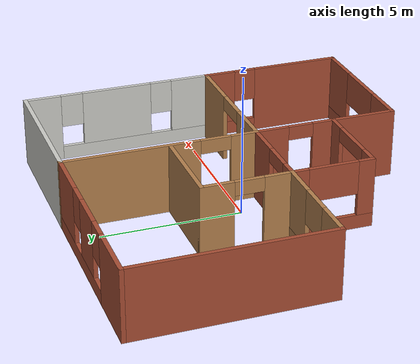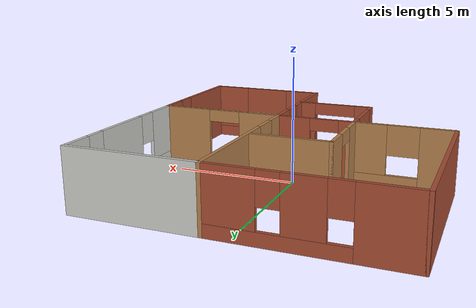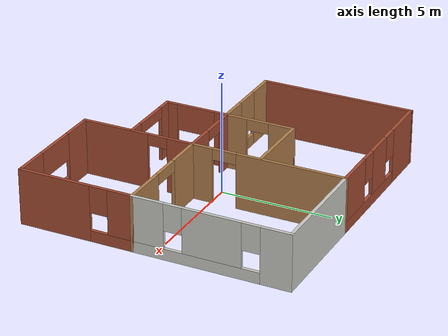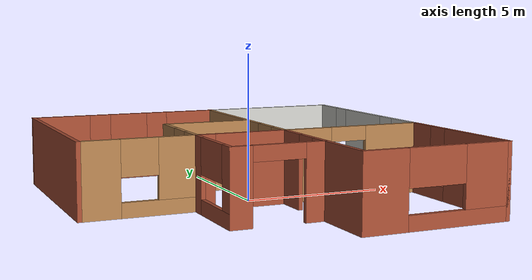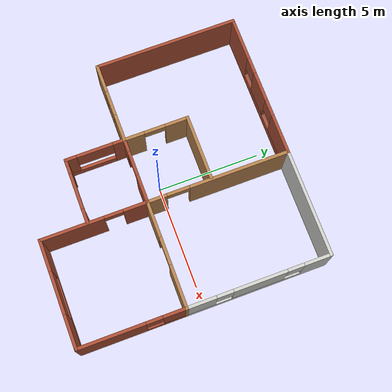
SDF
<?xml version='1.0'?>
<sdf version='1.7'>
  <model name='basic_house_model'>
    <link name='Wall_13'>
      <pose>-6.05 2.55 0 0 0 -1.5708</pose>
      <self_collide>0</self_collide>
      <enable_wind>0</enable_wind>
      <kinematic>0</kinematic>
      <visual name='Wall_13_Visual'>
        <pose>0 0 1.25 0 -0 0</pose>
        <geometry>
          <box>
            <size>7 0.15 2.5</size>
          </box>
        </geometry>
        <material>
          <script>
            <uri>file://media/materials/scripts/gazebo.material</uri>
            <name>Gazebo/Bricks</name>
          </script>
          <ambient>1 1 1 1</ambient>
          <shader type='pixel'/>
        </material>
        <meta>
          <layer>0</layer>
        </meta>
        <transparency>0</transparency>
        <cast_shadows>1</cast_shadows>
      </visual>
      <collision name='Wall_13_Collision'>
        <laser_retro>0</laser_retro>
        <max_contacts>10</max_contacts>
        <pose>0 0 1.25 0 -0 0</pose>
        <geometry>
          <box>
            <size>7 0.15 2.5</size>
          </box>
        </geometry>
        <surface>
          <friction>
            <ode>
              <mu>1</mu>
              <mu2>1</mu2>
              <fdir1>0 0 0</fdir1>
              <slip1>0</slip1>
              <slip2>0</slip2>
            </ode>
            <torsional>
              <coefficient>1</coefficient>
              <patch_radius>0</patch_radius>
              <surface_radius>0</surface_radius>
              <use_patch_radius>1</use_patch_radius>
              <ode>
                <slip>0</slip>
              </ode>
            </torsional>
          </friction>
          <bounce>
            <restitution_coefficient>0</restitution_coefficient>
            <threshold>1e+06</threshold>
          </bounce>
          <contact>
            <collide_without_contact>0</collide_without_contact>
            <collide_without_contact_bitmask>1</collide_without_contact_bitmask>
            <collide_bitmask>1</collide_bitmask>
            <ode>
              <soft_cfm>0</soft_cfm>
              <soft_erp>0.2</soft_erp>
              <kp>1e+13</kp>
              <kd>1</kd>
              <max_vel>0.01</max_vel>
              <min_depth>0</min_depth>
            </ode>
            <bullet>
              <split_impulse>1</split_impulse>
              <split_impulse_penetration_threshold>-0.01</split_impulse_penetration_threshold>
              <soft_cfm>0</soft_cfm>
              <soft_erp>0.2</soft_erp>
              <kp>1e+13</kp>
              <kd>1</kd>
            </bullet>
          </contact>
        </surface>
      </collision>
    </link>
    <link name='Wall_14'>
      <pose>-4.125 -0.875 0 0 -0 0</pose>
      <self_collide>0</self_collide>
      <enable_wind>0</enable_wind>
      <kinematic>0</kinematic>
      <visual name='Wall_14_Visual_0'>
        <pose>-1.30014 0 1.25 0 -0 0</pose>
        <geometry>
          <box>
            <size>1.39972 0.15 2.5</size>
          </box>
        </geometry>
        <material>
          <script>
            <uri>file://media/materials/scripts/gazebo.material</uri>
            <name>Gazebo/Wood</name>
          </script>
          <ambient>1 1 1 1</ambient>
          <shader type='pixel'/>
        </material>
        <meta>
          <layer>0</layer>
        </meta>
        <transparency>0</transparency>
        <cast_shadows>1</cast_shadows>
      </visual>
      <visual name='Wall_14_Visual_1'>
        <pose>0.699859 0 0.25 0 -0 0</pose>
        <geometry>
          <box>
            <size>2.60028 0.15 0.5</size>
          </box>
        </geometry>
        <material>
          <script>
            <uri>file://media/materials/scripts/gazebo.material</uri>
            <name>Gazebo/Wood</name>
          </script>
          <ambient>1 1 1 1</ambient>
          <shader type='pixel'/>
        </material>
        <meta>
          <layer>0</layer>
        </meta>
        <transparency>0</transparency>
        <cast_shadows>1</cast_shadows>
      </visual>
      <visual name='Wall_14_Visual_2'>
        <pose>1.31418 0 1.5 0 -0 0</pose>
        <geometry>
          <box>
            <size>1.37164 0.15 2</size>
          </box>
        </geometry>
        <material>
          <script>
            <uri>file://media/materials/scripts/gazebo.material</uri>
            <name>Gazebo/Wood</name>
          </script>
          <ambient>1 1 1 1</ambient>
          <shader type='pixel'/>
        </material>
        <meta>
          <layer>0</layer>
        </meta>
        <transparency>0</transparency>
        <cast_shadows>1</cast_shadows>
      </visual>
      <visual name='Wall_14_Visual_3'>
        <pose>0.014039 0 1.9 0 -0 0</pose>
        <geometry>
          <box>
            <size>1.22864 0.15 1.2</size>
          </box>
        </geometry>
        <material>
          <script>
            <uri>file://media/materials/scripts/gazebo.material</uri>
            <name>Gazebo/Wood</name>
          </script>
          <ambient>1 1 1 1</ambient>
          <shader type='pixel'/>
        </material>
        <meta>
          <layer>0</layer>
        </meta>
        <transparency>0</transparency>
        <cast_shadows>1</cast_shadows>
      </visual>
      <collision name='Wall_14_Collision_0'>
        <laser_retro>0</laser_retro>
        <max_contacts>10</max_contacts>
        <pose>-1.30014 0 1.25 0 -0 0</pose>
        <geometry>
          <box>
            <size>1.39972 0.15 2.5</size>
          </box>
        </geometry>
        <surface>
          <friction>
            <ode>
              <mu>1</mu>
              <mu2>1</mu2>
              <fdir1>0 0 0</fdir1>
              <slip1>0</slip1>
              <slip2>0</slip2>
            </ode>
            <torsional>
              <coefficient>1</coefficient>
              <patch_radius>0</patch_radius>
              <surface_radius>0</surface_radius>
              <use_patch_radius>1</use_patch_radius>
              <ode>
                <slip>0</slip>
              </ode>
            </torsional>
          </friction>
          <bounce>
            <restitution_coefficient>0</restitution_coefficient>
            <threshold>1e+06</threshold>
          </bounce>
          <contact>
            <collide_without_contact>0</collide_without_contact>
            <collide_without_contact_bitmask>1</collide_without_contact_bitmask>
            <collide_bitmask>1</collide_bitmask>
            <ode>
              <soft_cfm>0</soft_cfm>
              <soft_erp>0.2</soft_erp>
              <kp>1e+13</kp>
              <kd>1</kd>
              <max_vel>0.01</max_vel>
              <min_depth>0</min_depth>
            </ode>
            <bullet>
              <split_impulse>1</split_impulse>
              <split_impulse_penetration_threshold>-0.01</split_impulse_penetration_threshold>
              <soft_cfm>0</soft_cfm>
              <soft_erp>0.2</soft_erp>
              <kp>1e+13</kp>
              <kd>1</kd>
            </bullet>
          </contact>
        </surface>
      </collision>
      <collision name='Wall_14_Collision_1'>
        <laser_retro>0</laser_retro>
        <max_contacts>10</max_contacts>
        <pose>0.699859 0 0.25 0 -0 0</pose>
        <geometry>
          <box>
            <size>2.60028 0.15 0.5</size>
          </box>
        </geometry>
        <surface>
          <friction>
            <ode>
              <mu>1</mu>
              <mu2>1</mu2>
              <fdir1>0 0 0</fdir1>
              <slip1>0</slip1>
              <slip2>0</slip2>
            </ode>
            <torsional>
              <coefficient>1</coefficient>
              <patch_radius>0</patch_radius>
              <surface_radius>0</surface_radius>
              <use_patch_radius>1</use_patch_radius>
              <ode>
                <slip>0</slip>
              </ode>
            </torsional>
          </friction>
          <bounce>
            <restitution_coefficient>0</restitution_coefficient>
            <threshold>1e+06</threshold>
          </bounce>
          <contact>
            <collide_without_contact>0</collide_without_contact>
            <collide_without_contact_bitmask>1</collide_without_contact_bitmask>
            <collide_bitmask>1</collide_bitmask>
            <ode>
              <soft_cfm>0</soft_cfm>
              <soft_erp>0.2</soft_erp>
              <kp>1e+13</kp>
              <kd>1</kd>
              <max_vel>0.01</max_vel>
              <min_depth>0</min_depth>
            </ode>
            <bullet>
              <split_impulse>1</split_impulse>
              <split_impulse_penetration_threshold>-0.01</split_impulse_penetration_threshold>
              <soft_cfm>0</soft_cfm>
              <soft_erp>0.2</soft_erp>
              <kp>1e+13</kp>
              <kd>1</kd>
            </bullet>
          </contact>
        </surface>
      </collision>
      <collision name='Wall_14_Collision_2'>
        <laser_retro>0</laser_retro>
        <max_contacts>10</max_contacts>
        <pose>1.31418 0 1.5 0 -0 0</pose>
        <geometry>
          <box>
            <size>1.37164 0.15 2</size>
          </box>
        </geometry>
        <surface>
          <friction>
            <ode>
              <mu>1</mu>
              <mu2>1</mu2>
              <fdir1>0 0 0</fdir1>
              <slip1>0</slip1>
              <slip2>0</slip2>
            </ode>
            <torsional>
              <coefficient>1</coefficient>
              <patch_radius>0</patch_radius>
              <surface_radius>0</surface_radius>
              <use_patch_radius>1</use_patch_radius>
              <ode>
                <slip>0</slip>
              </ode>
            </torsional>
          </friction>
          <bounce>
            <restitution_coefficient>0</restitution_coefficient>
            <threshold>1e+06</threshold>
          </bounce>
          <contact>
            <collide_without_contact>0</collide_without_contact>
            <collide_without_contact_bitmask>1</collide_without_contact_bitmask>
            <collide_bitmask>1</collide_bitmask>
            <ode>
              <soft_cfm>0</soft_cfm>
              <soft_erp>0.2</soft_erp>
              <kp>1e+13</kp>
              <kd>1</kd>
              <max_vel>0.01</max_vel>
              <min_depth>0</min_depth>
            </ode>
            <bullet>
              <split_impulse>1</split_impulse>
              <split_impulse_penetration_threshold>-0.01</split_impulse_penetration_threshold>
              <soft_cfm>0</soft_cfm>
              <soft_erp>0.2</soft_erp>
              <kp>1e+13</kp>
              <kd>1</kd>
            </bullet>
          </contact>
        </surface>
      </collision>
      <collision name='Wall_14_Collision_3'>
        <laser_retro>0</laser_retro>
        <max_contacts>10</max_contacts>
        <pose>0.014039 0 1.9 0 -0 0</pose>
        <geometry>
          <box>
            <size>1.22864 0.15 1.2</size>
          </box>
        </geometry>
        <surface>
          <friction>
            <ode>
              <mu>1</mu>
              <mu2>1</mu2>
              <fdir1>0 0 0</fdir1>
              <slip1>0</slip1>
              <slip2>0</slip2>
            </ode>
            <torsional>
              <coefficient>1</coefficient>
              <patch_radius>0</patch_radius>
              <surface_radius>0</surface_radius>
              <use_patch_radius>1</use_patch_radius>
              <ode>
                <slip>0</slip>
              </ode>
            </torsional>
          </friction>
          <bounce>
            <restitution_coefficient>0</restitution_coefficient>
            <threshold>1e+06</threshold>
          </bounce>
          <contact>
            <collide_without_contact>0</collide_without_contact>
            <collide_without_contact_bitmask>1</collide_without_contact_bitmask>
            <collide_bitmask>1</collide_bitmask>
            <ode>
              <soft_cfm>0</soft_cfm>
              <soft_erp>0.2</soft_erp>
              <kp>1e+13</kp>
              <kd>1</kd>
              <max_vel>0.01</max_vel>
              <min_depth>0</min_depth>
            </ode>
            <bullet>
              <split_impulse>1</split_impulse>
              <split_impulse_penetration_threshold>-0.01</split_impulse_penetration_threshold>
              <soft_cfm>0</soft_cfm>
              <soft_erp>0.2</soft_erp>
              <kp>1e+13</kp>
              <kd>1</kd>
            </bullet>
          </contact>
        </surface>
      </collision>
    </link>
    <link name='Wall_15'>
      <pose>-2.2 0.675 0 0 -0 1.5708</pose>
      <self_collide>0</self_collide>
      <enable_wind>0</enable_wind>
      <kinematic>0</kinematic>
      <visual name='Wall_15_Visual_0'>
        <pose>-1.10266 0 1.25 0 -0 0</pose>
        <geometry>
          <box>
            <size>1.04468 0.15 2.5</size>
          </box>
        </geometry>
        <material>
          <script>
            <uri>file://media/materials/scripts/gazebo.material</uri>
            <name>Gazebo/Wood</name>
          </script>
          <ambient>1 1 1 1</ambient>
          <shader type='pixel'/>
        </material>
        <meta>
          <layer>0</layer>
        </meta>
        <transparency>0</transparency>
        <cast_shadows>1</cast_shadows>
      </visual>
      <visual name='Wall_15_Visual_1'>
        <pose>1.03215 0 1.25 0 -0 0</pose>
        <geometry>
          <box>
            <size>1.1857 0.15 2.5</size>
          </box>
        </geometry>
        <material>
          <script>
            <uri>file://media/materials/scripts/gazebo.material</uri>
            <name>Gazebo/Wood</name>
          </script>
          <ambient>1 1 1 1</ambient>
          <shader type='pixel'/>
        </material>
        <meta>
          <layer>0</layer>
        </meta>
        <transparency>0</transparency>
        <cast_shadows>1</cast_shadows>
      </visual>
      <visual name='Wall_15_Visual_2'>
        <pose>-0.070509 0 2.25 0 -0 0</pose>
        <geometry>
          <box>
            <size>1.01962 0.15 0.5</size>
          </box>
        </geometry>
        <material>
          <script>
            <uri>file://media/materials/scripts/gazebo.material</uri>
            <name>Gazebo/Wood</name>
          </script>
          <ambient>1 1 1 1</ambient>
          <shader type='pixel'/>
        </material>
        <meta>
          <layer>0</layer>
        </meta>
        <transparency>0</transparency>
        <cast_shadows>1</cast_shadows>
      </visual>
      <collision name='Wall_15_Collision_0'>
        <laser_retro>0</laser_retro>
        <max_contacts>10</max_contacts>
        <pose>-1.10266 0 1.25 0 -0 0</pose>
        <geometry>
          <box>
            <size>1.04468 0.15 2.5</size>
          </box>
        </geometry>
        <surface>
          <friction>
            <ode>
              <mu>1</mu>
              <mu2>1</mu2>
              <fdir1>0 0 0</fdir1>
              <slip1>0</slip1>
              <slip2>0</slip2>
            </ode>
            <torsional>
              <coefficient>1</coefficient>
              <patch_radius>0</patch_radius>
              <surface_radius>0</surface_radius>
              <use_patch_radius>1</use_patch_radius>
              <ode>
                <slip>0</slip>
              </ode>
            </torsional>
          </friction>
          <bounce>
            <restitution_coefficient>0</restitution_coefficient>
            <threshold>1e+06</threshold>
          </bounce>
          <contact>
            <collide_without_contact>0</collide_without_contact>
            <collide_without_contact_bitmask>1</collide_without_contact_bitmask>
            <collide_bitmask>1</collide_bitmask>
            <ode>
              <soft_cfm>0</soft_cfm>
              <soft_erp>0.2</soft_erp>
              <kp>1e+13</kp>
              <kd>1</kd>
              <max_vel>0.01</max_vel>
              <min_depth>0</min_depth>
            </ode>
            <bullet>
              <split_impulse>1</split_impulse>
              <split_impulse_penetration_threshold>-0.01</split_impulse_penetration_threshold>
              <soft_cfm>0</soft_cfm>
              <soft_erp>0.2</soft_erp>
              <kp>1e+13</kp>
              <kd>1</kd>
            </bullet>
          </contact>
        </surface>
      </collision>
      <collision name='Wall_15_Collision_1'>
        <laser_retro>0</laser_retro>
        <max_contacts>10</max_contacts>
        <pose>1.03215 0 1.25 0 -0 0</pose>
        <geometry>
          <box>
            <size>1.1857 0.15 2.5</size>
          </box>
        </geometry>
        <surface>
          <friction>
            <ode>
              <mu>1</mu>
              <mu2>1</mu2>
              <fdir1>0 0 0</fdir1>
              <slip1>0</slip1>
              <slip2>0</slip2>
            </ode>
            <torsional>
              <coefficient>1</coefficient>
              <patch_radius>0</patch_radius>
              <surface_radius>0</surface_radius>
              <use_patch_radius>1</use_patch_radius>
              <ode>
                <slip>0</slip>
              </ode>
            </torsional>
          </friction>
          <bounce>
            <restitution_coefficient>0</restitution_coefficient>
            <threshold>1e+06</threshold>
          </bounce>
          <contact>
            <collide_without_contact>0</collide_without_contact>
            <collide_without_contact_bitmask>1</collide_without_contact_bitmask>
            <collide_bitmask>1</collide_bitmask>
            <ode>
              <soft_cfm>0</soft_cfm>
              <soft_erp>0.2</soft_erp>
              <kp>1e+13</kp>
              <kd>1</kd>
              <max_vel>0.01</max_vel>
              <min_depth>0</min_depth>
            </ode>
            <bullet>
              <split_impulse>1</split_impulse>
              <split_impulse_penetration_threshold>-0.01</split_impulse_penetration_threshold>
              <soft_cfm>0</soft_cfm>
              <soft_erp>0.2</soft_erp>
              <kp>1e+13</kp>
              <kd>1</kd>
            </bullet>
          </contact>
        </surface>
      </collision>
      <collision name='Wall_15_Collision_2'>
        <laser_retro>0</laser_retro>
        <max_contacts>10</max_contacts>
        <pose>-0.070509 0 2.25 0 -0 0</pose>
        <geometry>
          <box>
            <size>1.01962 0.15 0.5</size>
          </box>
        </geometry>
        <surface>
          <friction>
            <ode>
              <mu>1</mu>
              <mu2>1</mu2>
              <fdir1>0 0 0</fdir1>
              <slip1>0</slip1>
              <slip2>0</slip2>
            </ode>
            <torsional>
              <coefficient>1</coefficient>
              <patch_radius>0</patch_radius>
              <surface_radius>0</surface_radius>
              <use_patch_radius>1</use_patch_radius>
              <ode>
                <slip>0</slip>
              </ode>
            </torsional>
          </friction>
          <bounce>
            <restitution_coefficient>0</restitution_coefficient>
            <threshold>1e+06</threshold>
          </bounce>
          <contact>
            <collide_without_contact>0</collide_without_contact>
            <collide_without_contact_bitmask>1</collide_without_contact_bitmask>
            <collide_bitmask>1</collide_bitmask>
            <ode>
              <soft_cfm>0</soft_cfm>
              <soft_erp>0.2</soft_erp>
              <kp>1e+13</kp>
              <kd>1</kd>
              <max_vel>0.01</max_vel>
              <min_depth>0</min_depth>
            </ode>
            <bullet>
              <split_impulse>1</split_impulse>
              <split_impulse_penetration_threshold>-0.01</split_impulse_penetration_threshold>
              <soft_cfm>0</soft_cfm>
              <soft_erp>0.2</soft_erp>
              <kp>1e+13</kp>
              <kd>1</kd>
            </bullet>
          </contact>
        </surface>
      </collision>
    </link>
    <link name='Wall_16'>
      <pose>-0.65 2.225 0 0 -0 0</pose>
      <self_collide>0</self_collide>
      <enable_wind>0</enable_wind>
      <kinematic>0</kinematic>
      <visual name='Wall_16_Visual'>
        <pose>0 0 1.25 0 -0 0</pose>
        <geometry>
          <box>
            <size>3.25 0.15 2.5</size>
          </box>
        </geometry>
        <material>
          <script>
            <uri>file://media/materials/scripts/gazebo.material</uri>
            <name>Gazebo/Wood</name>
          </script>
          <ambient>1 1 1 1</ambient>
          <shader type='pixel'/>
        </material>
        <meta>
          <layer>0</layer>
        </meta>
        <transparency>0</transparency>
        <cast_shadows>1</cast_shadows>
      </visual>
      <collision name='Wall_16_Collision'>
        <laser_retro>0</laser_retro>
        <max_contacts>10</max_contacts>
        <pose>0 0 1.25 0 -0 0</pose>
        <geometry>
          <box>
            <size>3.25 0.15 2.5</size>
          </box>
        </geometry>
        <surface>
          <friction>
            <ode>
              <mu>1</mu>
              <mu2>1</mu2>
              <fdir1>0 0 0</fdir1>
              <slip1>0</slip1>
              <slip2>0</slip2>
            </ode>
            <torsional>
              <coefficient>1</coefficient>
              <patch_radius>0</patch_radius>
              <surface_radius>0</surface_radius>
              <use_patch_radius>1</use_patch_radius>
              <ode>
                <slip>0</slip>
              </ode>
            </torsional>
          </friction>
          <bounce>
            <restitution_coefficient>0</restitution_coefficient>
            <threshold>1e+06</threshold>
          </bounce>
          <contact>
            <collide_without_contact>0</collide_without_contact>
            <collide_without_contact_bitmask>1</collide_without_contact_bitmask>
            <collide_bitmask>1</collide_bitmask>
            <ode>
              <soft_cfm>0</soft_cfm>
              <soft_erp>0.2</soft_erp>
              <kp>1e+13</kp>
              <kd>1</kd>
              <max_vel>0.01</max_vel>
              <min_depth>0</min_depth>
            </ode>
            <bullet>
              <split_impulse>1</split_impulse>
              <split_impulse_penetration_threshold>-0.01</split_impulse_penetration_threshold>
              <soft_cfm>0</soft_cfm>
              <soft_erp>0.2</soft_erp>
              <kp>1e+13</kp>
              <kd>1</kd>
            </bullet>
          </contact>
        </surface>
      </collision>
    </link>
    <link name='Wall_18'>
      <pose>-0.625 -0.875 0 0 -0 0</pose>
      <self_collide>0</self_collide>
      <enable_wind>0</enable_wind>
      <kinematic>0</kinematic>
      <visual name='Wall_18_Visual_0'>
        <pose>-1.3026 0 1.25 0 -0 0</pose>
        <geometry>
          <box>
            <size>0.694802 0.15 2.5</size>
          </box>
        </geometry>
        <material>
          <script>
            <uri>file://media/materials/scripts/gazebo.material</uri>
            <name>Gazebo/Bricks</name>
          </script>
          <ambient>1 1 1 1</ambient>
          <shader type='pixel'/>
        </material>
        <meta>
          <layer>0</layer>
        </meta>
        <transparency>0</transparency>
        <cast_shadows>1</cast_shadows>
      </visual>
      <visual name='Wall_18_Visual_1'>
        <pose>0.929233 0 1.25 0 -0 0</pose>
        <geometry>
          <box>
            <size>1.44153 0.15 2.5</size>
          </box>
        </geometry>
        <material>
          <script>
            <uri>file://media/materials/scripts/gazebo.material</uri>
            <name>Gazebo/Bricks</name>
          </script>
          <ambient>1 1 1 1</ambient>
          <shader type='pixel'/>
        </material>
        <meta>
          <layer>0</layer>
        </meta>
        <transparency>0</transparency>
        <cast_shadows>1</cast_shadows>
      </visual>
      <visual name='Wall_18_Visual_2'>
        <pose>-0.373366 0 2.25 0 -0 0</pose>
        <geometry>
          <box>
            <size>1.16366 0.15 0.5</size>
          </box>
        </geometry>
        <material>
          <script>
            <uri>file://media/materials/scripts/gazebo.material</uri>
            <name>Gazebo/Bricks</name>
          </script>
          <ambient>1 1 1 1</ambient>
          <shader type='pixel'/>
        </material>
        <meta>
          <layer>0</layer>
        </meta>
        <transparency>0</transparency>
        <cast_shadows>1</cast_shadows>
      </visual>
      <collision name='Wall_18_Collision_0'>
        <laser_retro>0</laser_retro>
        <max_contacts>10</max_contacts>
        <pose>-1.3026 0 1.25 0 -0 0</pose>
        <geometry>
          <box>
            <size>0.694802 0.15 2.5</size>
          </box>
        </geometry>
        <surface>
          <friction>
            <ode>
              <mu>1</mu>
              <mu2>1</mu2>
              <fdir1>0 0 0</fdir1>
              <slip1>0</slip1>
              <slip2>0</slip2>
            </ode>
            <torsional>
              <coefficient>1</coefficient>
              <patch_radius>0</patch_radius>
              <surface_radius>0</surface_radius>
              <use_patch_radius>1</use_patch_radius>
              <ode>
                <slip>0</slip>
              </ode>
            </torsional>
          </friction>
          <bounce>
            <restitution_coefficient>0</restitution_coefficient>
            <threshold>1e+06</threshold>
          </bounce>
          <contact>
            <collide_without_contact>0</collide_without_contact>
            <collide_without_contact_bitmask>1</collide_without_contact_bitmask>
            <collide_bitmask>1</collide_bitmask>
            <ode>
              <soft_cfm>0</soft_cfm>
              <soft_erp>0.2</soft_erp>
              <kp>1e+13</kp>
              <kd>1</kd>
              <max_vel>0.01</max_vel>
              <min_depth>0</min_depth>
            </ode>
            <bullet>
              <split_impulse>1</split_impulse>
              <split_impulse_penetration_threshold>-0.01</split_impulse_penetration_threshold>
              <soft_cfm>0</soft_cfm>
              <soft_erp>0.2</soft_erp>
              <kp>1e+13</kp>
              <kd>1</kd>
            </bullet>
          </contact>
        </surface>
      </collision>
      <collision name='Wall_18_Collision_1'>
        <laser_retro>0</laser_retro>
        <max_contacts>10</max_contacts>
        <pose>0.929233 0 1.25 0 -0 0</pose>
        <geometry>
          <box>
            <size>1.44153 0.15 2.5</size>
          </box>
        </geometry>
        <surface>
          <friction>
            <ode>
              <mu>1</mu>
              <mu2>1</mu2>
              <fdir1>0 0 0</fdir1>
              <slip1>0</slip1>
              <slip2>0</slip2>
            </ode>
            <torsional>
              <coefficient>1</coefficient>
              <patch_radius>0</patch_radius>
              <surface_radius>0</surface_radius>
              <use_patch_radius>1</use_patch_radius>
              <ode>
                <slip>0</slip>
              </ode>
            </torsional>
          </friction>
          <bounce>
            <restitution_coefficient>0</restitution_coefficient>
            <threshold>1e+06</threshold>
          </bounce>
          <contact>
            <collide_without_contact>0</collide_without_contact>
            <collide_without_contact_bitmask>1</collide_without_contact_bitmask>
            <collide_bitmask>1</collide_bitmask>
            <ode>
              <soft_cfm>0</soft_cfm>
              <soft_erp>0.2</soft_erp>
              <kp>1e+13</kp>
              <kd>1</kd>
              <max_vel>0.01</max_vel>
              <min_depth>0</min_depth>
            </ode>
            <bullet>
              <split_impulse>1</split_impulse>
              <split_impulse_penetration_threshold>-0.01</split_impulse_penetration_threshold>
              <soft_cfm>0</soft_cfm>
              <soft_erp>0.2</soft_erp>
              <kp>1e+13</kp>
              <kd>1</kd>
            </bullet>
          </contact>
        </surface>
      </collision>
      <collision name='Wall_18_Collision_2'>
        <laser_retro>0</laser_retro>
        <max_contacts>10</max_contacts>
        <pose>-0.373366 0 2.25 0 -0 0</pose>
        <geometry>
          <box>
            <size>1.16366 0.15 0.5</size>
          </box>
        </geometry>
        <surface>
          <friction>
            <ode>
              <mu>1</mu>
              <mu2>1</mu2>
              <fdir1>0 0 0</fdir1>
              <slip1>0</slip1>
              <slip2>0</slip2>
            </ode>
            <torsional>
              <coefficient>1</coefficient>
              <patch_radius>0</patch_radius>
              <surface_radius>0</surface_radius>
              <use_patch_radius>1</use_patch_radius>
              <ode>
                <slip>0</slip>
              </ode>
            </torsional>
          </friction>
          <bounce>
            <restitution_coefficient>0</restitution_coefficient>
            <threshold>1e+06</threshold>
          </bounce>
          <contact>
            <collide_without_contact>0</collide_without_contact>
            <collide_without_contact_bitmask>1</collide_without_contact_bitmask>
            <collide_bitmask>1</collide_bitmask>
            <ode>
              <soft_cfm>0</soft_cfm>
              <soft_erp>0.2</soft_erp>
              <kp>1e+13</kp>
              <kd>1</kd>
              <max_vel>0.01</max_vel>
              <min_depth>0</min_depth>
            </ode>
            <bullet>
              <split_impulse>1</split_impulse>
              <split_impulse_penetration_threshold>-0.01</split_impulse_penetration_threshold>
              <soft_cfm>0</soft_cfm>
              <soft_erp>0.2</soft_erp>
              <kp>1e+13</kp>
              <kd>1</kd>
            </bullet>
          </contact>
        </surface>
      </collision>
    </link>
    <link name='Wall_19'>
      <pose>0.95 -3.425 0 0 0 -1.5708</pose>
      <self_collide>0</self_collide>
      <enable_wind>0</enable_wind>
      <kinematic>0</kinematic>
      <visual name='Wall_19_Visual_0'>
        <pose>-2.00386 0 1.25 0 -0 0</pose>
        <geometry>
          <box>
            <size>1.24228 0.15 2.5</size>
          </box>
        </geometry>
        <material>
          <script>
            <uri>file://media/materials/scripts/gazebo.material</uri>
            <name>Gazebo/Bricks</name>
          </script>
          <ambient>1 1 1 1</ambient>
          <shader type='pixel'/>
        </material>
        <meta>
          <layer>0</layer>
        </meta>
        <transparency>0</transparency>
        <cast_shadows>1</cast_shadows>
      </visual>
      <visual name='Wall_19_Visual_1'>
        <pose>1.07114 0 1.25 0 -0 0</pose>
        <geometry>
          <box>
            <size>3.10772 0.15 2.5</size>
          </box>
        </geometry>
        <material>
          <script>
            <uri>file://media/materials/scripts/gazebo.material</uri>
            <name>Gazebo/Bricks</name>
          </script>
          <ambient>1 1 1 1</ambient>
          <shader type='pixel'/>
        </material>
        <meta>
          <layer>0</layer>
        </meta>
        <transparency>0</transparency>
        <cast_shadows>1</cast_shadows>
      </visual>
      <visual name='Wall_19_Visual_2'>
        <pose>-0.932718 0 2.25 0 -0 0</pose>
        <geometry>
          <box>
            <size>0.9 0.15 0.5</size>
          </box>
        </geometry>
        <material>
          <script>
            <uri>file://media/materials/scripts/gazebo.material</uri>
            <name>Gazebo/Bricks</name>
          </script>
          <ambient>1 1 1 1</ambient>
          <shader type='pixel'/>
        </material>
        <meta>
          <layer>0</layer>
        </meta>
        <transparency>0</transparency>
        <cast_shadows>1</cast_shadows>
      </visual>
      <collision name='Wall_19_Collision_0'>
        <laser_retro>0</laser_retro>
        <max_contacts>10</max_contacts>
        <pose>-2.00386 0 1.25 0 -0 0</pose>
        <geometry>
          <box>
            <size>1.24228 0.15 2.5</size>
          </box>
        </geometry>
        <surface>
          <friction>
            <ode>
              <mu>1</mu>
              <mu2>1</mu2>
              <fdir1>0 0 0</fdir1>
              <slip1>0</slip1>
              <slip2>0</slip2>
            </ode>
            <torsional>
              <coefficient>1</coefficient>
              <patch_radius>0</patch_radius>
              <surface_radius>0</surface_radius>
              <use_patch_radius>1</use_patch_radius>
              <ode>
                <slip>0</slip>
              </ode>
            </torsional>
          </friction>
          <bounce>
            <restitution_coefficient>0</restitution_coefficient>
            <threshold>1e+06</threshold>
          </bounce>
          <contact>
            <collide_without_contact>0</collide_without_contact>
            <collide_without_contact_bitmask>1</collide_without_contact_bitmask>
            <collide_bitmask>1</collide_bitmask>
            <ode>
              <soft_cfm>0</soft_cfm>
              <soft_erp>0.2</soft_erp>
              <kp>1e+13</kp>
              <kd>1</kd>
              <max_vel>0.01</max_vel>
              <min_depth>0</min_depth>
            </ode>
            <bullet>
              <split_impulse>1</split_impulse>
              <split_impulse_penetration_threshold>-0.01</split_impulse_penetration_threshold>
              <soft_cfm>0</soft_cfm>
              <soft_erp>0.2</soft_erp>
              <kp>1e+13</kp>
              <kd>1</kd>
            </bullet>
          </contact>
        </surface>
      </collision>
      <collision name='Wall_19_Collision_1'>
        <laser_retro>0</laser_retro>
        <max_contacts>10</max_contacts>
        <pose>1.07114 0 1.25 0 -0 0</pose>
        <geometry>
          <box>
            <size>3.10772 0.15 2.5</size>
          </box>
        </geometry>
        <surface>
          <friction>
            <ode>
              <mu>1</mu>
              <mu2>1</mu2>
              <fdir1>0 0 0</fdir1>
              <slip1>0</slip1>
              <slip2>0</slip2>
            </ode>
            <torsional>
              <coefficient>1</coefficient>
              <patch_radius>0</patch_radius>
              <surface_radius>0</surface_radius>
              <use_patch_radius>1</use_patch_radius>
              <ode>
                <slip>0</slip>
              </ode>
            </torsional>
          </friction>
          <bounce>
            <restitution_coefficient>0</restitution_coefficient>
            <threshold>1e+06</threshold>
          </bounce>
          <contact>
            <collide_without_contact>0</collide_without_contact>
            <collide_without_contact_bitmask>1</collide_without_contact_bitmask>
            <collide_bitmask>1</collide_bitmask>
            <ode>
              <soft_cfm>0</soft_cfm>
              <soft_erp>0.2</soft_erp>
              <kp>1e+13</kp>
              <kd>1</kd>
              <max_vel>0.01</max_vel>
              <min_depth>0</min_depth>
            </ode>
            <bullet>
              <split_impulse>1</split_impulse>
              <split_impulse_penetration_threshold>-0.01</split_impulse_penetration_threshold>
              <soft_cfm>0</soft_cfm>
              <soft_erp>0.2</soft_erp>
              <kp>1e+13</kp>
              <kd>1</kd>
            </bullet>
          </contact>
        </surface>
      </collision>
      <collision name='Wall_19_Collision_2'>
        <laser_retro>0</laser_retro>
        <max_contacts>10</max_contacts>
        <pose>-0.932718 0 2.25 0 -0 0</pose>
        <geometry>
          <box>
            <size>0.9 0.15 0.5</size>
          </box>
        </geometry>
        <surface>
          <friction>
            <ode>
              <mu>1</mu>
              <mu2>1</mu2>
              <fdir1>0 0 0</fdir1>
              <slip1>0</slip1>
              <slip2>0</slip2>
            </ode>
            <torsional>
              <coefficient>1</coefficient>
              <patch_radius>0</patch_radius>
              <surface_radius>0</surface_radius>
              <use_patch_radius>1</use_patch_radius>
              <ode>
                <slip>0</slip>
              </ode>
            </torsional>
          </friction>
          <bounce>
            <restitution_coefficient>0</restitution_coefficient>
            <threshold>1e+06</threshold>
          </bounce>
          <contact>
            <collide_without_contact>0</collide_without_contact>
            <collide_without_contact_bitmask>1</collide_without_contact_bitmask>
            <collide_bitmask>1</collide_bitmask>
            <ode>
              <soft_cfm>0</soft_cfm>
              <soft_erp>0.2</soft_erp>
              <kp>1e+13</kp>
              <kd>1</kd>
              <max_vel>0.01</max_vel>
              <min_depth>0</min_depth>
            </ode>
            <bullet>
              <split_impulse>1</split_impulse>
              <split_impulse_penetration_threshold>-0.01</split_impulse_penetration_threshold>
              <soft_cfm>0</soft_cfm>
              <soft_erp>0.2</soft_erp>
              <kp>1e+13</kp>
              <kd>1</kd>
            </bullet>
          </contact>
        </surface>
      </collision>
    </link>
    <link name='Wall_20'>
      <pose>3.5 -5.975 0 0 -0 0</pose>
      <self_collide>0</self_collide>
      <enable_wind>0</enable_wind>
      <kinematic>0</kinematic>
      <visual name='Wall_20_Visual_0'>
        <pose>-1.83971 0 1.25 0 -0 0</pose>
        <geometry>
          <box>
            <size>1.57058 0.15 2.5</size>
          </box>
        </geometry>
        <material>
          <script>
            <uri>file://media/materials/scripts/gazebo.material</uri>
            <name>Gazebo/Bricks</name>
          </script>
          <ambient>1 1 1 1</ambient>
          <shader type='pixel'/>
        </material>
        <meta>
          <layer>0</layer>
        </meta>
        <transparency>0</transparency>
        <cast_shadows>1</cast_shadows>
      </visual>
      <visual name='Wall_20_Visual_1'>
        <pose>0.785288 0 0.25 0 -0 0</pose>
        <geometry>
          <box>
            <size>3.67943 0.15 0.5</size>
          </box>
        </geometry>
        <material>
          <script>
            <uri>file://media/materials/scripts/gazebo.material</uri>
            <name>Gazebo/Bricks</name>
          </script>
          <ambient>1 1 1 1</ambient>
          <shader type='pixel'/>
        </material>
        <meta>
          <layer>0</layer>
        </meta>
        <transparency>0</transparency>
        <cast_shadows>1</cast_shadows>
      </visual>
      <visual name='Wall_20_Visual_2'>
        <pose>1.79171 0 1.5 0 -0 0</pose>
        <geometry>
          <box>
            <size>1.66657 0.15 2</size>
          </box>
        </geometry>
        <material>
          <script>
            <uri>file://media/materials/scripts/gazebo.material</uri>
            <name>Gazebo/Bricks</name>
          </script>
          <ambient>1 1 1 1</ambient>
          <shader type='pixel'/>
        </material>
        <meta>
          <layer>0</layer>
        </meta>
        <transparency>0</transparency>
        <cast_shadows>1</cast_shadows>
      </visual>
      <visual name='Wall_20_Visual_3'>
        <pose>-0.047998 0 1.9 0 -0 0</pose>
        <geometry>
          <box>
            <size>2.01285 0.15 1.2</size>
          </box>
        </geometry>
        <material>
          <script>
            <uri>file://media/materials/scripts/gazebo.material</uri>
            <name>Gazebo/Bricks</name>
          </script>
          <ambient>1 1 1 1</ambient>
          <shader type='pixel'/>
        </material>
        <meta>
          <layer>0</layer>
        </meta>
        <transparency>0</transparency>
        <cast_shadows>1</cast_shadows>
      </visual>
      <collision name='Wall_20_Collision_0'>
        <laser_retro>0</laser_retro>
        <max_contacts>10</max_contacts>
        <pose>-1.83971 0 1.25 0 -0 0</pose>
        <geometry>
          <box>
            <size>1.57058 0.15 2.5</size>
          </box>
        </geometry>
        <surface>
          <friction>
            <ode>
              <mu>1</mu>
              <mu2>1</mu2>
              <fdir1>0 0 0</fdir1>
              <slip1>0</slip1>
              <slip2>0</slip2>
            </ode>
            <torsional>
              <coefficient>1</coefficient>
              <patch_radius>0</patch_radius>
              <surface_radius>0</surface_radius>
              <use_patch_radius>1</use_patch_radius>
              <ode>
                <slip>0</slip>
              </ode>
            </torsional>
          </friction>
          <bounce>
            <restitution_coefficient>0</restitution_coefficient>
            <threshold>1e+06</threshold>
          </bounce>
          <contact>
            <collide_without_contact>0</collide_without_contact>
            <collide_without_contact_bitmask>1</collide_without_contact_bitmask>
            <collide_bitmask>1</collide_bitmask>
            <ode>
              <soft_cfm>0</soft_cfm>
              <soft_erp>0.2</soft_erp>
              <kp>1e+13</kp>
              <kd>1</kd>
              <max_vel>0.01</max_vel>
              <min_depth>0</min_depth>
            </ode>
            <bullet>
              <split_impulse>1</split_impulse>
              <split_impulse_penetration_threshold>-0.01</split_impulse_penetration_threshold>
              <soft_cfm>0</soft_cfm>
              <soft_erp>0.2</soft_erp>
              <kp>1e+13</kp>
              <kd>1</kd>
            </bullet>
          </contact>
        </surface>
      </collision>
      <collision name='Wall_20_Collision_2'>
        <laser_retro>0</laser_retro>
        <max_contacts>10</max_contacts>
        <pose>1.79171 0 1.5 0 -0 0</pose>
        <geometry>
          <box>
            <size>1.66657 0.15 2</size>
          </box>
        </geometry>
        <surface>
          <friction>
            <ode>
              <mu>1</mu>
              <mu2>1</mu2>
              <fdir1>0 0 0</fdir1>
              <slip1>0</slip1>
              <slip2>0</slip2>
            </ode>
            <torsional>
              <coefficient>1</coefficient>
              <patch_radius>0</patch_radius>
              <surface_radius>0</surface_radius>
              <use_patch_radius>1</use_patch_radius>
              <ode>
                <slip>0</slip>
              </ode>
            </torsional>
          </friction>
          <bounce>
            <restitution_coefficient>0</restitution_coefficient>
            <threshold>1e+06</threshold>
          </bounce>
          <contact>
            <collide_without_contact>0</collide_without_contact>
            <collide_without_contact_bitmask>1</collide_without_contact_bitmask>
            <collide_bitmask>1</collide_bitmask>
            <ode>
              <soft_cfm>0</soft_cfm>
              <soft_erp>0.2</soft_erp>
              <kp>1e+13</kp>
              <kd>1</kd>
              <max_vel>0.01</max_vel>
              <min_depth>0</min_depth>
            </ode>
            <bullet>
              <split_impulse>1</split_impulse>
              <split_impulse_penetration_threshold>-0.01</split_impulse_penetration_threshold>
              <soft_cfm>0</soft_cfm>
              <soft_erp>0.2</soft_erp>
              <kp>1e+13</kp>
              <kd>1</kd>
            </bullet>
          </contact>
        </surface>
      </collision>
      <collision name='Wall_20_Collision_1'>
        <laser_retro>0</laser_retro>
        <max_contacts>10</max_contacts>
        <pose>0.785288 0 0.25 0 -0 0</pose>
        <geometry>
          <box>
            <size>3.67943 0.15 0.5</size>
          </box>
        </geometry>
        <surface>
          <friction>
            <ode>
              <mu>1</mu>
              <mu2>1</mu2>
              <fdir1>0 0 0</fdir1>
              <slip1>0</slip1>
              <slip2>0</slip2>
            </ode>
            <torsional>
              <coefficient>1</coefficient>
              <patch_radius>0</patch_radius>
              <surface_radius>0</surface_radius>
              <use_patch_radius>1</use_patch_radius>
              <ode>
                <slip>0</slip>
              </ode>
            </torsional>
          </friction>
          <bounce>
            <restitution_coefficient>0</restitution_coefficient>
            <threshold>1e+06</threshold>
          </bounce>
          <contact>
            <collide_without_contact>0</collide_without_contact>
            <collide_without_contact_bitmask>1</collide_without_contact_bitmask>
            <collide_bitmask>1</collide_bitmask>
            <ode>
              <soft_cfm>0</soft_cfm>
              <soft_erp>0.2</soft_erp>
              <kp>1e+13</kp>
              <kd>1</kd>
              <max_vel>0.01</max_vel>
              <min_depth>0</min_depth>
            </ode>
            <bullet>
              <split_impulse>1</split_impulse>
              <split_impulse_penetration_threshold>-0.01</split_impulse_penetration_threshold>
              <soft_cfm>0</soft_cfm>
              <soft_erp>0.2</soft_erp>
              <kp>1e+13</kp>
              <kd>1</kd>
            </bullet>
          </contact>
        </surface>
      </collision>
      <collision name='Wall_20_Collision_3'>
        <laser_retro>0</laser_retro>
        <max_contacts>10</max_contacts>
        <pose>-0.047998 0 1.9 0 -0 0</pose>
        <geometry>
          <box>
            <size>2.01285 0.15 1.2</size>
          </box>
        </geometry>
        <surface>
          <friction>
            <ode>
              <mu>1</mu>
              <mu2>1</mu2>
              <fdir1>0 0 0</fdir1>
              <slip1>0</slip1>
              <slip2>0</slip2>
            </ode>
            <torsional>
              <coefficient>1</coefficient>
              <patch_radius>0</patch_radius>
              <surface_radius>0</surface_radius>
              <use_patch_radius>1</use_patch_radius>
              <ode>
                <slip>0</slip>
              </ode>
            </torsional>
          </friction>
          <bounce>
            <restitution_coefficient>0</restitution_coefficient>
            <threshold>1e+06</threshold>
          </bounce>
          <contact>
            <collide_without_contact>0</collide_without_contact>
            <collide_without_contact_bitmask>1</collide_without_contact_bitmask>
            <collide_bitmask>1</collide_bitmask>
            <ode>
              <soft_cfm>0</soft_cfm>
              <soft_erp>0.2</soft_erp>
              <kp>1e+13</kp>
              <kd>1</kd>
              <max_vel>0.01</max_vel>
              <min_depth>0</min_depth>
            </ode>
            <bullet>
              <split_impulse>1</split_impulse>
              <split_impulse_penetration_threshold>-0.01</split_impulse_penetration_threshold>
              <soft_cfm>0</soft_cfm>
              <soft_erp>0.2</soft_erp>
              <kp>1e+13</kp>
              <kd>1</kd>
            </bullet>
          </contact>
        </surface>
      </collision>
    </link>
    <link name='Wall_21'>
      <pose>6.05 -3.425 0 0 -0 1.5708</pose>
      <self_collide>0</self_collide>
      <enable_wind>0</enable_wind>
      <kinematic>0</kinematic>
      <visual name='Wall_21_Visual_0'>
        <pose>-0.987562 0 1.25 0 -0 0</pose>
        <geometry>
          <box>
            <size>3.27488 0.15 2.5</size>
          </box>
        </geometry>
        <material>
          <script>
            <uri>file://media/materials/scripts/gazebo.material</uri>
            <name>Gazebo/Bricks</name>
          </script>
          <ambient>1 1 1 1</ambient>
          <shader type='pixel'/>
        </material>
        <meta>
          <layer>0</layer>
        </meta>
        <transparency>0</transparency>
        <cast_shadows>1</cast_shadows>
      </visual>
      <visual name='Wall_21_Visual_1'>
        <pose>1.63744 0 0.25 0 -0 0</pose>
        <geometry>
          <box>
            <size>1.97512 0.15 0.5</size>
          </box>
        </geometry>
        <material>
          <script>
            <uri>file://media/materials/scripts/gazebo.material</uri>
            <name>Gazebo/Bricks</name>
          </script>
          <ambient>1 1 1 1</ambient>
          <shader type='pixel'/>
        </material>
        <meta>
          <layer>0</layer>
        </meta>
        <transparency>0</transparency>
        <cast_shadows>1</cast_shadows>
      </visual>
      <visual name='Wall_21_Visual_2'>
        <pose>2.03744 0 1.5 0 -0 0</pose>
        <geometry>
          <box>
            <size>1.17512 0.15 2</size>
          </box>
        </geometry>
        <material>
          <script>
            <uri>file://media/materials/scripts/gazebo.material</uri>
            <name>Gazebo/Bricks</name>
          </script>
          <ambient>1 1 1 1</ambient>
          <shader type='pixel'/>
        </material>
        <meta>
          <layer>0</layer>
        </meta>
        <transparency>0</transparency>
        <cast_shadows>1</cast_shadows>
      </visual>
      <visual name='Wall_21_Visual_3'>
        <pose>1.04988 0 1.9 0 -0 0</pose>
        <geometry>
          <box>
            <size>0.8 0.15 1.2</size>
          </box>
        </geometry>
        <material>
          <script>
            <uri>file://media/materials/scripts/gazebo.material</uri>
            <name>Gazebo/Bricks</name>
          </script>
          <ambient>1 1 1 1</ambient>
          <shader type='pixel'/>
        </material>
        <meta>
          <layer>0</layer>
        </meta>
        <transparency>0</transparency>
        <cast_shadows>1</cast_shadows>
      </visual>
      <collision name='Wall_21_Collision_3'>
        <laser_retro>0</laser_retro>
        <max_contacts>10</max_contacts>
        <pose>1.04988 0 1.9 0 -0 0</pose>
        <geometry>
          <box>
            <size>0.8 0.15 1.2</size>
          </box>
        </geometry>
        <surface>
          <friction>
            <ode>
              <mu>1</mu>
              <mu2>1</mu2>
              <fdir1>0 0 0</fdir1>
              <slip1>0</slip1>
              <slip2>0</slip2>
            </ode>
            <torsional>
              <coefficient>1</coefficient>
              <patch_radius>0</patch_radius>
              <surface_radius>0</surface_radius>
              <use_patch_radius>1</use_patch_radius>
              <ode>
                <slip>0</slip>
              </ode>
            </torsional>
          </friction>
          <bounce>
            <restitution_coefficient>0</restitution_coefficient>
            <threshold>1e+06</threshold>
          </bounce>
          <contact>
            <collide_without_contact>0</collide_without_contact>
            <collide_without_contact_bitmask>1</collide_without_contact_bitmask>
            <collide_bitmask>1</collide_bitmask>
            <ode>
              <soft_cfm>0</soft_cfm>
              <soft_erp>0.2</soft_erp>
              <kp>1e+13</kp>
              <kd>1</kd>
              <max_vel>0.01</max_vel>
              <min_depth>0</min_depth>
            </ode>
            <bullet>
              <split_impulse>1</split_impulse>
              <split_impulse_penetration_threshold>-0.01</split_impulse_penetration_threshold>
              <soft_cfm>0</soft_cfm>
              <soft_erp>0.2</soft_erp>
              <kp>1e+13</kp>
              <kd>1</kd>
            </bullet>
          </contact>
        </surface>
      </collision>
      <collision name='Wall_21_Collision_0'>
        <laser_retro>0</laser_retro>
        <max_contacts>10</max_contacts>
        <pose>-0.987562 0 1.25 0 -0 0</pose>
        <geometry>
          <box>
            <size>3.27488 0.15 2.5</size>
          </box>
        </geometry>
        <surface>
          <friction>
            <ode>
              <mu>1</mu>
              <mu2>1</mu2>
              <fdir1>0 0 0</fdir1>
              <slip1>0</slip1>
              <slip2>0</slip2>
            </ode>
            <torsional>
              <coefficient>1</coefficient>
              <patch_radius>0</patch_radius>
              <surface_radius>0</surface_radius>
              <use_patch_radius>1</use_patch_radius>
              <ode>
                <slip>0</slip>
              </ode>
            </torsional>
          </friction>
          <bounce>
            <restitution_coefficient>0</restitution_coefficient>
            <threshold>1e+06</threshold>
          </bounce>
          <contact>
            <collide_without_contact>0</collide_without_contact>
            <collide_without_contact_bitmask>1</collide_without_contact_bitmask>
            <collide_bitmask>1</collide_bitmask>
            <ode>
              <soft_cfm>0</soft_cfm>
              <soft_erp>0.2</soft_erp>
              <kp>1e+13</kp>
              <kd>1</kd>
              <max_vel>0.01</max_vel>
              <min_depth>0</min_depth>
            </ode>
            <bullet>
              <split_impulse>1</split_impulse>
              <split_impulse_penetration_threshold>-0.01</split_impulse_penetration_threshold>
              <soft_cfm>0</soft_cfm>
              <soft_erp>0.2</soft_erp>
              <kp>1e+13</kp>
              <kd>1</kd>
            </bullet>
          </contact>
        </surface>
      </collision>
      <collision name='Wall_21_Collision_1'>
        <laser_retro>0</laser_retro>
        <max_contacts>10</max_contacts>
        <pose>1.63744 0 0.25 0 -0 0</pose>
        <geometry>
          <box>
            <size>1.97512 0.15 0.5</size>
          </box>
        </geometry>
        <surface>
          <friction>
            <ode>
              <mu>1</mu>
              <mu2>1</mu2>
              <fdir1>0 0 0</fdir1>
              <slip1>0</slip1>
              <slip2>0</slip2>
            </ode>
            <torsional>
              <coefficient>1</coefficient>
              <patch_radius>0</patch_radius>
              <surface_radius>0</surface_radius>
              <use_patch_radius>1</use_patch_radius>
              <ode>
                <slip>0</slip>
              </ode>
            </torsional>
          </friction>
          <bounce>
            <restitution_coefficient>0</restitution_coefficient>
            <threshold>1e+06</threshold>
          </bounce>
          <contact>
            <collide_without_contact>0</collide_without_contact>
            <collide_without_contact_bitmask>1</collide_without_contact_bitmask>
            <collide_bitmask>1</collide_bitmask>
            <ode>
              <soft_cfm>0</soft_cfm>
              <soft_erp>0.2</soft_erp>
              <kp>1e+13</kp>
              <kd>1</kd>
              <max_vel>0.01</max_vel>
              <min_depth>0</min_depth>
            </ode>
            <bullet>
              <split_impulse>1</split_impulse>
              <split_impulse_penetration_threshold>-0.01</split_impulse_penetration_threshold>
              <soft_cfm>0</soft_cfm>
              <soft_erp>0.2</soft_erp>
              <kp>1e+13</kp>
              <kd>1</kd>
            </bullet>
          </contact>
        </surface>
      </collision>
      <collision name='Wall_21_Collision_2'>
        <laser_retro>0</laser_retro>
        <max_contacts>10</max_contacts>
        <pose>2.03744 0 1.5 0 -0 0</pose>
        <geometry>
          <box>
            <size>1.17512 0.15 2</size>
          </box>
        </geometry>
        <surface>
          <friction>
            <ode>
              <mu>1</mu>
              <mu2>1</mu2>
              <fdir1>0 0 0</fdir1>
              <slip1>0</slip1>
              <slip2>0</slip2>
            </ode>
            <torsional>
              <coefficient>1</coefficient>
              <patch_radius>0</patch_radius>
              <surface_radius>0</surface_radius>
              <use_patch_radius>1</use_patch_radius>
              <ode>
                <slip>0</slip>
              </ode>
            </torsional>
          </friction>
          <bounce>
            <restitution_coefficient>0</restitution_coefficient>
            <threshold>1e+06</threshold>
          </bounce>
          <contact>
            <collide_without_contact>0</collide_without_contact>
            <collide_without_contact_bitmask>1</collide_without_contact_bitmask>
            <collide_bitmask>1</collide_bitmask>
            <ode>
              <soft_cfm>0</soft_cfm>
              <soft_erp>0.2</soft_erp>
              <kp>1e+13</kp>
              <kd>1</kd>
              <max_vel>0.01</max_vel>
              <min_depth>0</min_depth>
            </ode>
            <bullet>
              <split_impulse>1</split_impulse>
              <split_impulse_penetration_threshold>-0.01</split_impulse_penetration_threshold>
              <soft_cfm>0</soft_cfm>
              <soft_erp>0.2</soft_erp>
              <kp>1e+13</kp>
              <kd>1</kd>
            </bullet>
          </contact>
        </surface>
      </collision>
    </link>
    <link name='Wall_23'>
      <pose>-2.2 -2.3 0 0 0 -1.5708</pose>
      <self_collide>0</self_collide>
      <enable_wind>0</enable_wind>
      <kinematic>0</kinematic>
      <visual name='Wall_23_Visual_0'>
        <pose>-1.1761 0 1.25 0 -0 0</pose>
        <geometry>
          <box>
            <size>0.647796 0.15 2.5</size>
          </box>
        </geometry>
        <material>
          <script>
            <uri>file://media/materials/scripts/gazebo.material</uri>
            <name>Gazebo/Bricks</name>
          </script>
          <ambient>1 1 1 1</ambient>
          <shader type='pixel'/>
        </material>
        <meta>
          <layer>0</layer>
        </meta>
        <transparency>0</transparency>
        <cast_shadows>1</cast_shadows>
      </visual>
      <visual name='Wall_23_Visual_1'>
        <pose>0.323898 0 0.25 0 -0 0</pose>
        <geometry>
          <box>
            <size>2.3522 0.15 0.5</size>
          </box>
        </geometry>
        <material>
          <script>
            <uri>file://media/materials/scripts/gazebo.material</uri>
            <name>Gazebo/Bricks</name>
          </script>
          <ambient>1 1 1 1</ambient>
          <shader type='pixel'/>
        </material>
        <meta>
          <layer>0</layer>
        </meta>
        <transparency>0</transparency>
        <cast_shadows>1</cast_shadows>
      </visual>
      <visual name='Wall_23_Visual_2'>
        <pose>1.20508 0 1.5 0 -0 0</pose>
        <geometry>
          <box>
            <size>0.589831 0.15 2</size>
          </box>
        </geometry>
        <material>
          <script>
            <uri>file://media/materials/scripts/gazebo.material</uri>
            <name>Gazebo/Bricks</name>
          </script>
          <ambient>1 1 1 1</ambient>
          <shader type='pixel'/>
        </material>
        <meta>
          <layer>0</layer>
        </meta>
        <transparency>0</transparency>
        <cast_shadows>1</cast_shadows>
      </visual>
      <visual name='Wall_23_Visual_3'>
        <pose>0.028983 0 1.9 0 -0 0</pose>
        <geometry>
          <box>
            <size>1.76237 0.15 1.2</size>
          </box>
        </geometry>
        <material>
          <script>
            <uri>file://media/materials/scripts/gazebo.material</uri>
            <name>Gazebo/Bricks</name>
          </script>
          <ambient>1 1 1 1</ambient>
          <shader type='pixel'/>
        </material>
        <meta>
          <layer>0</layer>
        </meta>
        <transparency>0</transparency>
        <cast_shadows>1</cast_shadows>
      </visual>
      <collision name='Wall_23_Collision_0'>
        <laser_retro>0</laser_retro>
        <max_contacts>10</max_contacts>
        <pose>-1.1761 0 1.25 0 -0 0</pose>
        <geometry>
          <box>
            <size>0.647796 0.15 2.5</size>
          </box>
        </geometry>
        <surface>
          <friction>
            <ode>
              <mu>1</mu>
              <mu2>1</mu2>
              <fdir1>0 0 0</fdir1>
              <slip1>0</slip1>
              <slip2>0</slip2>
            </ode>
            <torsional>
              <coefficient>1</coefficient>
              <patch_radius>0</patch_radius>
              <surface_radius>0</surface_radius>
              <use_patch_radius>1</use_patch_radius>
              <ode>
                <slip>0</slip>
              </ode>
            </torsional>
          </friction>
          <bounce>
            <restitution_coefficient>0</restitution_coefficient>
            <threshold>1e+06</threshold>
          </bounce>
          <contact>
            <collide_without_contact>0</collide_without_contact>
            <collide_without_contact_bitmask>1</collide_without_contact_bitmask>
            <collide_bitmask>1</collide_bitmask>
            <ode>
              <soft_cfm>0</soft_cfm>
              <soft_erp>0.2</soft_erp>
              <kp>1e+13</kp>
              <kd>1</kd>
              <max_vel>0.01</max_vel>
              <min_depth>0</min_depth>
            </ode>
            <bullet>
              <split_impulse>1</split_impulse>
              <split_impulse_penetration_threshold>-0.01</split_impulse_penetration_threshold>
              <soft_cfm>0</soft_cfm>
              <soft_erp>0.2</soft_erp>
              <kp>1e+13</kp>
              <kd>1</kd>
            </bullet>
          </contact>
        </surface>
      </collision>
      <collision name='Wall_23_Collision_1'>
        <laser_retro>0</laser_retro>
        <max_contacts>10</max_contacts>
        <pose>0.323898 0 0.25 0 -0 0</pose>
        <geometry>
          <box>
            <size>2.3522 0.15 0.5</size>
          </box>
        </geometry>
        <surface>
          <friction>
            <ode>
              <mu>1</mu>
              <mu2>1</mu2>
              <fdir1>0 0 0</fdir1>
              <slip1>0</slip1>
              <slip2>0</slip2>
            </ode>
            <torsional>
              <coefficient>1</coefficient>
              <patch_radius>0</patch_radius>
              <surface_radius>0</surface_radius>
              <use_patch_radius>1</use_patch_radius>
              <ode>
                <slip>0</slip>
              </ode>
            </torsional>
          </friction>
          <bounce>
            <restitution_coefficient>0</restitution_coefficient>
            <threshold>1e+06</threshold>
          </bounce>
          <contact>
            <collide_without_contact>0</collide_without_contact>
            <collide_without_contact_bitmask>1</collide_without_contact_bitmask>
            <collide_bitmask>1</collide_bitmask>
            <ode>
              <soft_cfm>0</soft_cfm>
              <soft_erp>0.2</soft_erp>
              <kp>1e+13</kp>
              <kd>1</kd>
              <max_vel>0.01</max_vel>
              <min_depth>0</min_depth>
            </ode>
            <bullet>
              <split_impulse>1</split_impulse>
              <split_impulse_penetration_threshold>-0.01</split_impulse_penetration_threshold>
              <soft_cfm>0</soft_cfm>
              <soft_erp>0.2</soft_erp>
              <kp>1e+13</kp>
              <kd>1</kd>
            </bullet>
          </contact>
        </surface>
      </collision>
      <collision name='Wall_23_Collision_2'>
        <laser_retro>0</laser_retro>
        <max_contacts>10</max_contacts>
        <pose>1.20508 0 1.5 0 -0 0</pose>
        <geometry>
          <box>
            <size>0.589831 0.15 2</size>
          </box>
        </geometry>
        <surface>
          <friction>
            <ode>
              <mu>1</mu>
              <mu2>1</mu2>
              <fdir1>0 0 0</fdir1>
              <slip1>0</slip1>
              <slip2>0</slip2>
            </ode>
            <torsional>
              <coefficient>1</coefficient>
              <patch_radius>0</patch_radius>
              <surface_radius>0</surface_radius>
              <use_patch_radius>1</use_patch_radius>
              <ode>
                <slip>0</slip>
              </ode>
            </torsional>
          </friction>
          <bounce>
            <restitution_coefficient>0</restitution_coefficient>
            <threshold>1e+06</threshold>
          </bounce>
          <contact>
            <collide_without_contact>0</collide_without_contact>
            <collide_without_contact_bitmask>1</collide_without_contact_bitmask>
            <collide_bitmask>1</collide_bitmask>
            <ode>
              <soft_cfm>0</soft_cfm>
              <soft_erp>0.2</soft_erp>
              <kp>1e+13</kp>
              <kd>1</kd>
              <max_vel>0.01</max_vel>
              <min_depth>0</min_depth>
            </ode>
            <bullet>
              <split_impulse>1</split_impulse>
              <split_impulse_penetration_threshold>-0.01</split_impulse_penetration_threshold>
              <soft_cfm>0</soft_cfm>
              <soft_erp>0.2</soft_erp>
              <kp>1e+13</kp>
              <kd>1</kd>
            </bullet>
          </contact>
        </surface>
      </collision>
      <collision name='Wall_23_Collision_3'>
        <laser_retro>0</laser_retro>
        <max_contacts>10</max_contacts>
        <pose>0.028983 0 1.9 0 -0 0</pose>
        <geometry>
          <box>
            <size>1.76237 0.15 1.2</size>
          </box>
        </geometry>
        <surface>
          <friction>
            <ode>
              <mu>1</mu>
              <mu2>1</mu2>
              <fdir1>0 0 0</fdir1>
              <slip1>0</slip1>
              <slip2>0</slip2>
            </ode>
            <torsional>
              <coefficient>1</coefficient>
              <patch_radius>0</patch_radius>
              <surface_radius>0</surface_radius>
              <use_patch_radius>1</use_patch_radius>
              <ode>
                <slip>0</slip>
              </ode>
            </torsional>
          </friction>
          <bounce>
            <restitution_coefficient>0</restitution_coefficient>
            <threshold>1e+06</threshold>
          </bounce>
          <contact>
            <collide_without_contact>0</collide_without_contact>
            <collide_without_contact_bitmask>1</collide_without_contact_bitmask>
            <collide_bitmask>1</collide_bitmask>
            <ode>
              <soft_cfm>0</soft_cfm>
              <soft_erp>0.2</soft_erp>
              <kp>1e+13</kp>
              <kd>1</kd>
              <max_vel>0.01</max_vel>
              <min_depth>0</min_depth>
            </ode>
            <bullet>
              <split_impulse>1</split_impulse>
              <split_impulse_penetration_threshold>-0.01</split_impulse_penetration_threshold>
              <soft_cfm>0</soft_cfm>
              <soft_erp>0.2</soft_erp>
              <kp>1e+13</kp>
              <kd>1</kd>
            </bullet>
          </contact>
        </surface>
      </collision>
    </link>
    <link name='Wall_24'>
      <pose>-0.65 -3.725 0 0 -0 0</pose>
      <self_collide>0</self_collide>
      <enable_wind>0</enable_wind>
      <kinematic>0</kinematic>
      <visual name='Wall_24_Visual_0'>
        <pose>-1.24412 0 1.25 0 -0 0</pose>
        <geometry>
          <box>
            <size>0.761761 0.15 2.5</size>
          </box>
        </geometry>
        <material>
          <script>
            <uri>file://media/materials/scripts/gazebo.material</uri>
            <name>Gazebo/Bricks</name>
          </script>
          <ambient>1 1 1 1</ambient>
          <shader type='pixel'/>
        </material>
        <meta>
          <layer>0</layer>
        </meta>
        <transparency>0</transparency>
        <cast_shadows>1</cast_shadows>
      </visual>
      <visual name='Wall_24_Visual_1'>
        <pose>1.25933 0 1.25 0 -0 0</pose>
        <geometry>
          <box>
            <size>0.731332 0.15 2.5</size>
          </box>
        </geometry>
        <material>
          <script>
            <uri>file://media/materials/scripts/gazebo.material</uri>
            <name>Gazebo/Bricks</name>
          </script>
          <ambient>1 1 1 1</ambient>
          <shader type='pixel'/>
        </material>
        <meta>
          <layer>0</layer>
        </meta>
        <transparency>0</transparency>
        <cast_shadows>1</cast_shadows>
      </visual>
      <visual name='Wall_24_Visual_2'>
        <pose>0.015215 0 2.25 0 -0 0</pose>
        <geometry>
          <box>
            <size>1.75691 0.15 0.5</size>
          </box>
        </geometry>
        <material>
          <script>
            <uri>file://media/materials/scripts/gazebo.material</uri>
            <name>Gazebo/Bricks</name>
          </script>
          <ambient>1 1 1 1</ambient>
          <shader type='pixel'/>
        </material>
        <meta>
          <layer>0</layer>
        </meta>
        <transparency>0</transparency>
        <cast_shadows>1</cast_shadows>
      </visual>
      <collision name='Wall_24_Collision_0'>
        <laser_retro>0</laser_retro>
        <max_contacts>10</max_contacts>
        <pose>-1.24412 0 1.25 0 -0 0</pose>
        <geometry>
          <box>
            <size>0.761761 0.15 2.5</size>
          </box>
        </geometry>
        <surface>
          <friction>
            <ode>
              <mu>1</mu>
              <mu2>1</mu2>
              <fdir1>0 0 0</fdir1>
              <slip1>0</slip1>
              <slip2>0</slip2>
            </ode>
            <torsional>
              <coefficient>1</coefficient>
              <patch_radius>0</patch_radius>
              <surface_radius>0</surface_radius>
              <use_patch_radius>1</use_patch_radius>
              <ode>
                <slip>0</slip>
              </ode>
            </torsional>
          </friction>
          <bounce>
            <restitution_coefficient>0</restitution_coefficient>
            <threshold>1e+06</threshold>
          </bounce>
          <contact>
            <collide_without_contact>0</collide_without_contact>
            <collide_without_contact_bitmask>1</collide_without_contact_bitmask>
            <collide_bitmask>1</collide_bitmask>
            <ode>
              <soft_cfm>0</soft_cfm>
              <soft_erp>0.2</soft_erp>
              <kp>1e+13</kp>
              <kd>1</kd>
              <max_vel>0.01</max_vel>
              <min_depth>0</min_depth>
            </ode>
            <bullet>
              <split_impulse>1</split_impulse>
              <split_impulse_penetration_threshold>-0.01</split_impulse_penetration_threshold>
              <soft_cfm>0</soft_cfm>
              <soft_erp>0.2</soft_erp>
              <kp>1e+13</kp>
              <kd>1</kd>
            </bullet>
          </contact>
        </surface>
      </collision>
      <collision name='Wall_24_Collision_1'>
        <laser_retro>0</laser_retro>
        <max_contacts>10</max_contacts>
        <pose>1.25933 0 1.25 0 -0 0</pose>
        <geometry>
          <box>
            <size>0.731332 0.15 2.5</size>
          </box>
        </geometry>
        <surface>
          <friction>
            <ode>
              <mu>1</mu>
              <mu2>1</mu2>
              <fdir1>0 0 0</fdir1>
              <slip1>0</slip1>
              <slip2>0</slip2>
            </ode>
            <torsional>
              <coefficient>1</coefficient>
              <patch_radius>0</patch_radius>
              <surface_radius>0</surface_radius>
              <use_patch_radius>1</use_patch_radius>
              <ode>
                <slip>0</slip>
              </ode>
            </torsional>
          </friction>
          <bounce>
            <restitution_coefficient>0</restitution_coefficient>
            <threshold>1e+06</threshold>
          </bounce>
          <contact>
            <collide_without_contact>0</collide_without_contact>
            <collide_without_contact_bitmask>1</collide_without_contact_bitmask>
            <collide_bitmask>1</collide_bitmask>
            <ode>
              <soft_cfm>0</soft_cfm>
              <soft_erp>0.2</soft_erp>
              <kp>1e+13</kp>
              <kd>1</kd>
              <max_vel>0.01</max_vel>
              <min_depth>0</min_depth>
            </ode>
            <bullet>
              <split_impulse>1</split_impulse>
              <split_impulse_penetration_threshold>-0.01</split_impulse_penetration_threshold>
              <soft_cfm>0</soft_cfm>
              <soft_erp>0.2</soft_erp>
              <kp>1e+13</kp>
              <kd>1</kd>
            </bullet>
          </contact>
        </surface>
      </collision>
      <collision name='Wall_24_Collision_2'>
        <laser_retro>0</laser_retro>
        <max_contacts>10</max_contacts>
        <pose>0.015215 0 2.25 0 -0 0</pose>
        <geometry>
          <box>
            <size>1.75691 0.15 0.5</size>
          </box>
        </geometry>
        <surface>
          <friction>
            <ode>
              <mu>1</mu>
              <mu2>1</mu2>
              <fdir1>0 0 0</fdir1>
              <slip1>0</slip1>
              <slip2>0</slip2>
            </ode>
            <torsional>
              <coefficient>1</coefficient>
              <patch_radius>0</patch_radius>
              <surface_radius>0</surface_radius>
              <use_patch_radius>1</use_patch_radius>
              <ode>
                <slip>0</slip>
              </ode>
            </torsional>
          </friction>
          <bounce>
            <restitution_coefficient>0</restitution_coefficient>
            <threshold>1e+06</threshold>
          </bounce>
          <contact>
            <collide_without_contact>0</collide_without_contact>
            <collide_without_contact_bitmask>1</collide_without_contact_bitmask>
            <collide_bitmask>1</collide_bitmask>
            <ode>
              <soft_cfm>0</soft_cfm>
              <soft_erp>0.2</soft_erp>
              <kp>1e+13</kp>
              <kd>1</kd>
              <max_vel>0.01</max_vel>
              <min_depth>0</min_depth>
            </ode>
            <bullet>
              <split_impulse>1</split_impulse>
              <split_impulse_penetration_threshold>-0.01</split_impulse_penetration_threshold>
              <soft_cfm>0</soft_cfm>
              <soft_erp>0.2</soft_erp>
              <kp>1e+13</kp>
              <kd>1</kd>
            </bullet>
          </contact>
        </surface>
      </collision>
    </link>
    <link name='Wall_26'>
      <pose>-2.55 5.975 0 0 -0 0</pose>
      <self_collide>0</self_collide>
      <enable_wind>0</enable_wind>
      <kinematic>0</kinematic>
      <visual name='Wall_26_Visual_0'>
        <pose>-2.49982 0 1.25 0 -0 0</pose>
        <geometry>
          <box>
            <size>2.15036 0.15 2.5</size>
          </box>
        </geometry>
        <material>
          <script>
            <uri>file://media/materials/scripts/gazebo.material</uri>
            <name>Gazebo/Bricks</name>
          </script>
          <ambient>1 1 1 1</ambient>
          <shader type='pixel'/>
        </material>
        <meta>
          <layer>0</layer>
        </meta>
        <transparency>0</transparency>
        <cast_shadows>1</cast_shadows>
      </visual>
      <visual name='Wall_26_Visual_1'>
        <pose>1.07518 0 0.25 0 -0 0</pose>
        <geometry>
          <box>
            <size>4.99964 0.15 0.5</size>
          </box>
        </geometry>
        <material>
          <script>
            <uri>file://media/materials/scripts/gazebo.material</uri>
            <name>Gazebo/Bricks</name>
          </script>
          <ambient>1 1 1 1</ambient>
          <shader type='pixel'/>
        </material>
        <meta>
          <layer>0</layer>
        </meta>
        <transparency>0</transparency>
        <cast_shadows>1</cast_shadows>
      </visual>
      <visual name='Wall_26_Visual_2'>
        <pose>0.095935 0 1.5 0 -0 0</pose>
        <geometry>
          <box>
            <size>1.44114 0.15 2</size>
          </box>
        </geometry>
        <material>
          <script>
            <uri>file://media/materials/scripts/gazebo.material</uri>
            <name>Gazebo/Bricks</name>
          </script>
          <ambient>1 1 1 1</ambient>
          <shader type='pixel'/>
        </material>
        <meta>
          <layer>0</layer>
        </meta>
        <transparency>0</transparency>
        <cast_shadows>1</cast_shadows>
      </visual>
      <visual name='Wall_26_Visual_3'>
        <pose>2.59575 0 1.5 0 -0 0</pose>
        <geometry>
          <box>
            <size>1.95849 0.15 2</size>
          </box>
        </geometry>
        <material>
          <script>
            <uri>file://media/materials/scripts/gazebo.material</uri>
            <name>Gazebo/Bricks</name>
          </script>
          <ambient>1 1 1 1</ambient>
          <shader type='pixel'/>
        </material>
        <meta>
          <layer>0</layer>
        </meta>
        <transparency>0</transparency>
        <cast_shadows>1</cast_shadows>
      </visual>
      <visual name='Wall_26_Visual_4'>
        <pose>-1.02464 0 1.9 0 -0 0</pose>
        <geometry>
          <box>
            <size>0.8 0.15 1.2</size>
          </box>
        </geometry>
        <material>
          <script>
            <uri>file://media/materials/scripts/gazebo.material</uri>
            <name>Gazebo/Bricks</name>
          </script>
          <ambient>1 1 1 1</ambient>
          <shader type='pixel'/>
        </material>
        <meta>
          <layer>0</layer>
        </meta>
        <transparency>0</transparency>
        <cast_shadows>1</cast_shadows>
      </visual>
      <visual name='Wall_26_Visual_5'>
        <pose>1.21651 0 1.9 0 -0 0</pose>
        <geometry>
          <box>
            <size>0.8 0.15 1.2</size>
          </box>
        </geometry>
        <material>
          <script>
            <uri>file://media/materials/scripts/gazebo.material</uri>
            <name>Gazebo/Bricks</name>
          </script>
          <ambient>1 1 1 1</ambient>
          <shader type='pixel'/>
        </material>
        <meta>
          <layer>0</layer>
        </meta>
        <transparency>0</transparency>
        <cast_shadows>1</cast_shadows>
      </visual>
      <collision name='Wall_26_Collision_0'>
        <laser_retro>0</laser_retro>
        <max_contacts>10</max_contacts>
        <pose>-2.49982 0 1.25 0 -0 0</pose>
        <geometry>
          <box>
            <size>2.15036 0.15 2.5</size>
          </box>
        </geometry>
        <surface>
          <friction>
            <ode>
              <mu>1</mu>
              <mu2>1</mu2>
              <fdir1>0 0 0</fdir1>
              <slip1>0</slip1>
              <slip2>0</slip2>
            </ode>
            <torsional>
              <coefficient>1</coefficient>
              <patch_radius>0</patch_radius>
              <surface_radius>0</surface_radius>
              <use_patch_radius>1</use_patch_radius>
              <ode>
                <slip>0</slip>
              </ode>
            </torsional>
          </friction>
          <bounce>
            <restitution_coefficient>0</restitution_coefficient>
            <threshold>1e+06</threshold>
          </bounce>
          <contact>
            <collide_without_contact>0</collide_without_contact>
            <collide_without_contact_bitmask>1</collide_without_contact_bitmask>
            <collide_bitmask>1</collide_bitmask>
            <ode>
              <soft_cfm>0</soft_cfm>
              <soft_erp>0.2</soft_erp>
              <kp>1e+13</kp>
              <kd>1</kd>
              <max_vel>0.01</max_vel>
              <min_depth>0</min_depth>
            </ode>
            <bullet>
              <split_impulse>1</split_impulse>
              <split_impulse_penetration_threshold>-0.01</split_impulse_penetration_threshold>
              <soft_cfm>0</soft_cfm>
              <soft_erp>0.2</soft_erp>
              <kp>1e+13</kp>
              <kd>1</kd>
            </bullet>
          </contact>
        </surface>
      </collision>
      <collision name='Wall_26_Collision_1'>
        <laser_retro>0</laser_retro>
        <max_contacts>10</max_contacts>
        <pose>1.07518 0 0.25 0 -0 0</pose>
        <geometry>
          <box>
            <size>4.99964 0.15 0.5</size>
          </box>
        </geometry>
        <surface>
          <friction>
            <ode>
              <mu>1</mu>
              <mu2>1</mu2>
              <fdir1>0 0 0</fdir1>
              <slip1>0</slip1>
              <slip2>0</slip2>
            </ode>
            <torsional>
              <coefficient>1</coefficient>
              <patch_radius>0</patch_radius>
              <surface_radius>0</surface_radius>
              <use_patch_radius>1</use_patch_radius>
              <ode>
                <slip>0</slip>
              </ode>
            </torsional>
          </friction>
          <bounce>
            <restitution_coefficient>0</restitution_coefficient>
            <threshold>1e+06</threshold>
          </bounce>
          <contact>
            <collide_without_contact>0</collide_without_contact>
            <collide_without_contact_bitmask>1</collide_without_contact_bitmask>
            <collide_bitmask>1</collide_bitmask>
            <ode>
              <soft_cfm>0</soft_cfm>
              <soft_erp>0.2</soft_erp>
              <kp>1e+13</kp>
              <kd>1</kd>
              <max_vel>0.01</max_vel>
              <min_depth>0</min_depth>
            </ode>
            <bullet>
              <split_impulse>1</split_impulse>
              <split_impulse_penetration_threshold>-0.01</split_impulse_penetration_threshold>
              <soft_cfm>0</soft_cfm>
              <soft_erp>0.2</soft_erp>
              <kp>1e+13</kp>
              <kd>1</kd>
            </bullet>
          </contact>
        </surface>
      </collision>
      <collision name='Wall_26_Collision_2'>
        <laser_retro>0</laser_retro>
        <max_contacts>10</max_contacts>
        <pose>0.095935 0 1.5 0 -0 0</pose>
        <geometry>
          <box>
            <size>1.44114 0.15 2</size>
          </box>
        </geometry>
        <surface>
          <friction>
            <ode>
              <mu>1</mu>
              <mu2>1</mu2>
              <fdir1>0 0 0</fdir1>
              <slip1>0</slip1>
              <slip2>0</slip2>
            </ode>
            <torsional>
              <coefficient>1</coefficient>
              <patch_radius>0</patch_radius>
              <surface_radius>0</surface_radius>
              <use_patch_radius>1</use_patch_radius>
              <ode>
                <slip>0</slip>
              </ode>
            </torsional>
          </friction>
          <bounce>
            <restitution_coefficient>0</restitution_coefficient>
            <threshold>1e+06</threshold>
          </bounce>
          <contact>
            <collide_without_contact>0</collide_without_contact>
            <collide_without_contact_bitmask>1</collide_without_contact_bitmask>
            <collide_bitmask>1</collide_bitmask>
            <ode>
              <soft_cfm>0</soft_cfm>
              <soft_erp>0.2</soft_erp>
              <kp>1e+13</kp>
              <kd>1</kd>
              <max_vel>0.01</max_vel>
              <min_depth>0</min_depth>
            </ode>
            <bullet>
              <split_impulse>1</split_impulse>
              <split_impulse_penetration_threshold>-0.01</split_impulse_penetration_threshold>
              <soft_cfm>0</soft_cfm>
              <soft_erp>0.2</soft_erp>
              <kp>1e+13</kp>
              <kd>1</kd>
            </bullet>
          </contact>
        </surface>
      </collision>
      <collision name='Wall_26_Collision_3'>
        <laser_retro>0</laser_retro>
        <max_contacts>10</max_contacts>
        <pose>2.59575 0 1.5 0 -0 0</pose>
        <geometry>
          <box>
            <size>1.95849 0.15 2</size>
          </box>
        </geometry>
        <surface>
          <friction>
            <ode>
              <mu>1</mu>
              <mu2>1</mu2>
              <fdir1>0 0 0</fdir1>
              <slip1>0</slip1>
              <slip2>0</slip2>
            </ode>
            <torsional>
              <coefficient>1</coefficient>
              <patch_radius>0</patch_radius>
              <surface_radius>0</surface_radius>
              <use_patch_radius>1</use_patch_radius>
              <ode>
                <slip>0</slip>
              </ode>
            </torsional>
          </friction>
          <bounce>
            <restitution_coefficient>0</restitution_coefficient>
            <threshold>1e+06</threshold>
          </bounce>
          <contact>
            <collide_without_contact>0</collide_without_contact>
            <collide_without_contact_bitmask>1</collide_without_contact_bitmask>
            <collide_bitmask>1</collide_bitmask>
            <ode>
              <soft_cfm>0</soft_cfm>
              <soft_erp>0.2</soft_erp>
              <kp>1e+13</kp>
              <kd>1</kd>
              <max_vel>0.01</max_vel>
              <min_depth>0</min_depth>
            </ode>
            <bullet>
              <split_impulse>1</split_impulse>
              <split_impulse_penetration_threshold>-0.01</split_impulse_penetration_threshold>
              <soft_cfm>0</soft_cfm>
              <soft_erp>0.2</soft_erp>
              <kp>1e+13</kp>
              <kd>1</kd>
            </bullet>
          </contact>
        </surface>
      </collision>
      <collision name='Wall_26_Collision_5'>
        <laser_retro>0</laser_retro>
        <max_contacts>10</max_contacts>
        <pose>1.21651 0 1.9 0 -0 0</pose>
        <geometry>
          <box>
            <size>0.8 0.15 1.2</size>
          </box>
        </geometry>
        <surface>
          <friction>
            <ode>
              <mu>1</mu>
              <mu2>1</mu2>
              <fdir1>0 0 0</fdir1>
              <slip1>0</slip1>
              <slip2>0</slip2>
            </ode>
            <torsional>
              <coefficient>1</coefficient>
              <patch_radius>0</patch_radius>
              <surface_radius>0</surface_radius>
              <use_patch_radius>1</use_patch_radius>
              <ode>
                <slip>0</slip>
              </ode>
            </torsional>
          </friction>
          <bounce>
            <restitution_coefficient>0</restitution_coefficient>
            <threshold>1e+06</threshold>
          </bounce>
          <contact>
            <collide_without_contact>0</collide_without_contact>
            <collide_without_contact_bitmask>1</collide_without_contact_bitmask>
            <collide_bitmask>1</collide_bitmask>
            <ode>
              <soft_cfm>0</soft_cfm>
              <soft_erp>0.2</soft_erp>
              <kp>1e+13</kp>
              <kd>1</kd>
              <max_vel>0.01</max_vel>
              <min_depth>0</min_depth>
            </ode>
            <bullet>
              <split_impulse>1</split_impulse>
              <split_impulse_penetration_threshold>-0.01</split_impulse_penetration_threshold>
              <soft_cfm>0</soft_cfm>
              <soft_erp>0.2</soft_erp>
              <kp>1e+13</kp>
              <kd>1</kd>
            </bullet>
          </contact>
        </surface>
      </collision>
      <collision name='Wall_26_Collision_4'>
        <laser_retro>0</laser_retro>
        <max_contacts>10</max_contacts>
        <pose>-1.02464 0 1.9 0 -0 0</pose>
        <geometry>
          <box>
            <size>0.8 0.15 1.2</size>
          </box>
        </geometry>
        <surface>
          <friction>
            <ode>
              <mu>1</mu>
              <mu2>1</mu2>
              <fdir1>0 0 0</fdir1>
              <slip1>0</slip1>
              <slip2>0</slip2>
            </ode>
            <torsional>
              <coefficient>1</coefficient>
              <patch_radius>0</patch_radius>
              <surface_radius>0</surface_radius>
              <use_patch_radius>1</use_patch_radius>
              <ode>
                <slip>0</slip>
              </ode>
            </torsional>
          </friction>
          <bounce>
            <restitution_coefficient>0</restitution_coefficient>
            <threshold>1e+06</threshold>
          </bounce>
          <contact>
            <collide_without_contact>0</collide_without_contact>
            <collide_without_contact_bitmask>1</collide_without_contact_bitmask>
            <collide_bitmask>1</collide_bitmask>
            <ode>
              <soft_cfm>0</soft_cfm>
              <soft_erp>0.2</soft_erp>
              <kp>1e+13</kp>
              <kd>1</kd>
              <max_vel>0.01</max_vel>
              <min_depth>0</min_depth>
            </ode>
            <bullet>
              <split_impulse>1</split_impulse>
              <split_impulse_penetration_threshold>-0.01</split_impulse_penetration_threshold>
              <soft_cfm>0</soft_cfm>
              <soft_erp>0.2</soft_erp>
              <kp>1e+13</kp>
              <kd>1</kd>
            </bullet>
          </contact>
        </surface>
      </collision>
    </link>
    <link name='Wall_27'>
      <pose>3.5 5.975 0 0 -0 0</pose>
      <self_collide>0</self_collide>
      <enable_wind>0</enable_wind>
      <kinematic>0</kinematic>
      <visual name='Wall_27_Visual'>
        <pose>0 0 1.25 0 -0 0</pose>
        <geometry>
          <box>
            <size>5.25 0.15 2.5</size>
          </box>
        </geometry>
        <material>
          <script>
            <uri>file://media/materials/scripts/gazebo.material</uri>
            <name>Gazebo/CeilingTiled</name>
          </script>
          <ambient>1 1 1 1</ambient>
          <shader type='pixel'/>
        </material>
        <meta>
          <layer>0</layer>
        </meta>
        <transparency>0</transparency>
        <cast_shadows>1</cast_shadows>
      </visual>
      <collision name='Wall_27_Collision'>
        <laser_retro>0</laser_retro>
        <max_contacts>10</max_contacts>
        <pose>0 0 1.25 0 -0 0</pose>
        <geometry>
          <box>
            <size>5.25 0.15 2.5</size>
          </box>
        </geometry>
        <surface>
          <friction>
            <ode>
              <mu>1</mu>
              <mu2>1</mu2>
              <fdir1>0 0 0</fdir1>
              <slip1>0</slip1>
              <slip2>0</slip2>
            </ode>
            <torsional>
              <coefficient>1</coefficient>
              <patch_radius>0</patch_radius>
              <surface_radius>0</surface_radius>
              <use_patch_radius>1</use_patch_radius>
              <ode>
                <slip>0</slip>
              </ode>
            </torsional>
          </friction>
          <bounce>
            <restitution_coefficient>0</restitution_coefficient>
            <threshold>1e+06</threshold>
          </bounce>
          <contact>
            <collide_without_contact>0</collide_without_contact>
            <collide_without_contact_bitmask>1</collide_without_contact_bitmask>
            <collide_bitmask>1</collide_bitmask>
            <ode>
              <soft_cfm>0</soft_cfm>
              <soft_erp>0.2</soft_erp>
              <kp>1e+13</kp>
              <kd>1</kd>
              <max_vel>0.01</max_vel>
              <min_depth>0</min_depth>
            </ode>
            <bullet>
              <split_impulse>1</split_impulse>
              <split_impulse_penetration_threshold>-0.01</split_impulse_penetration_threshold>
              <soft_cfm>0</soft_cfm>
              <soft_erp>0.2</soft_erp>
              <kp>1e+13</kp>
              <kd>1</kd>
            </bullet>
          </contact>
        </surface>
      </collision>
    </link>
    <link name='Wall_6'>
      <pose>6.05 2.55 0 0 0 -1.5708</pose>
      <self_collide>0</self_collide>
      <enable_wind>0</enable_wind>
      <kinematic>0</kinematic>
      <visual name='Wall_6_Visual_0'>
        <pose>-2.82309 0 1.25 0 -0 0</pose>
        <geometry>
          <box>
            <size>1.35381 0.15 2.5</size>
          </box>
        </geometry>
        <material>
          <script>
            <uri>file://media/materials/scripts/gazebo.material</uri>
            <name>Gazebo/CeilingTiled</name>
          </script>
          <ambient>1 1 1 1</ambient>
          <shader type='pixel'/>
        </material>
        <meta>
          <layer>0</layer>
        </meta>
        <transparency>0</transparency>
        <cast_shadows>1</cast_shadows>
      </visual>
      <visual name='Wall_6_Visual_1'>
        <pose>0.676907 0 0.25 0 -0 0</pose>
        <geometry>
          <box>
            <size>5.64619 0.15 0.5</size>
          </box>
        </geometry>
        <material>
          <script>
            <uri>file://media/materials/scripts/gazebo.material</uri>
            <name>Gazebo/CeilingTiled</name>
          </script>
          <ambient>1 1 1 1</ambient>
          <shader type='pixel'/>
        </material>
        <meta>
          <layer>0</layer>
        </meta>
        <transparency>0</transparency>
        <cast_shadows>1</cast_shadows>
      </visual>
      <visual name='Wall_6_Visual_2'>
        <pose>-0.061529 0 1.5 0 -0 0</pose>
        <geometry>
          <box>
            <size>2.56931 0.15 2</size>
          </box>
        </geometry>
        <material>
          <script>
            <uri>file://media/materials/scripts/gazebo.material</uri>
            <name>Gazebo/CeilingTiled</name>
          </script>
          <ambient>1 1 1 1</ambient>
          <shader type='pixel'/>
        </material>
        <meta>
          <layer>0</layer>
        </meta>
        <transparency>0</transparency>
        <cast_shadows>1</cast_shadows>
      </visual>
      <visual name='Wall_6_Visual_3'>
        <pose>2.76156 0 1.5 0 -0 0</pose>
        <geometry>
          <box>
            <size>1.47687 0.15 2</size>
          </box>
        </geometry>
        <material>
          <script>
            <uri>file://media/materials/scripts/gazebo.material</uri>
            <name>Gazebo/CeilingTiled</name>
          </script>
          <ambient>1 1 1 1</ambient>
          <shader type='pixel'/>
        </material>
        <meta>
          <layer>0</layer>
        </meta>
        <transparency>0</transparency>
        <cast_shadows>1</cast_shadows>
      </visual>
      <visual name='Wall_6_Visual_4'>
        <pose>-1.74619 0 1.9 0 -0 0</pose>
        <geometry>
          <box>
            <size>0.8 0.15 1.2</size>
          </box>
        </geometry>
        <material>
          <script>
            <uri>file://media/materials/scripts/gazebo.material</uri>
            <name>Gazebo/CeilingTiled</name>
          </script>
          <ambient>1 1 1 1</ambient>
          <shader type='pixel'/>
        </material>
        <meta>
          <layer>0</layer>
        </meta>
        <transparency>0</transparency>
        <cast_shadows>1</cast_shadows>
      </visual>
      <visual name='Wall_6_Visual_5'>
        <pose>1.62313 0 1.9 0 -0 0</pose>
        <geometry>
          <box>
            <size>0.8 0.15 1.2</size>
          </box>
        </geometry>
        <material>
          <script>
            <uri>file://media/materials/scripts/gazebo.material</uri>
            <name>Gazebo/CeilingTiled</name>
          </script>
          <ambient>1 1 1 1</ambient>
          <shader type='pixel'/>
        </material>
        <meta>
          <layer>0</layer>
        </meta>
        <transparency>0</transparency>
        <cast_shadows>1</cast_shadows>
      </visual>
      <collision name='Wall_6_Collision_0'>
        <laser_retro>0</laser_retro>
        <max_contacts>10</max_contacts>
        <pose>-2.82309 0 1.25 0 -0 0</pose>
        <geometry>
          <box>
            <size>1.35381 0.15 2.5</size>
          </box>
        </geometry>
        <surface>
          <friction>
            <ode>
              <mu>1</mu>
              <mu2>1</mu2>
              <fdir1>0 0 0</fdir1>
              <slip1>0</slip1>
              <slip2>0</slip2>
            </ode>
            <torsional>
              <coefficient>1</coefficient>
              <patch_radius>0</patch_radius>
              <surface_radius>0</surface_radius>
              <use_patch_radius>1</use_patch_radius>
              <ode>
                <slip>0</slip>
              </ode>
            </torsional>
          </friction>
          <bounce>
            <restitution_coefficient>0</restitution_coefficient>
            <threshold>1e+06</threshold>
          </bounce>
          <contact>
            <collide_without_contact>0</collide_without_contact>
            <collide_without_contact_bitmask>1</collide_without_contact_bitmask>
            <collide_bitmask>1</collide_bitmask>
            <ode>
              <soft_cfm>0</soft_cfm>
              <soft_erp>0.2</soft_erp>
              <kp>1e+13</kp>
              <kd>1</kd>
              <max_vel>0.01</max_vel>
              <min_depth>0</min_depth>
            </ode>
            <bullet>
              <split_impulse>1</split_impulse>
              <split_impulse_penetration_threshold>-0.01</split_impulse_penetration_threshold>
              <soft_cfm>0</soft_cfm>
              <soft_erp>0.2</soft_erp>
              <kp>1e+13</kp>
              <kd>1</kd>
            </bullet>
          </contact>
        </surface>
      </collision>
      <collision name='Wall_6_Collision_1'>
        <laser_retro>0</laser_retro>
        <max_contacts>10</max_contacts>
        <pose>0.676907 0 0.25 0 -0 0</pose>
        <geometry>
          <box>
            <size>5.64619 0.15 0.5</size>
          </box>
        </geometry>
        <surface>
          <friction>
            <ode>
              <mu>1</mu>
              <mu2>1</mu2>
              <fdir1>0 0 0</fdir1>
              <slip1>0</slip1>
              <slip2>0</slip2>
            </ode>
            <torsional>
              <coefficient>1</coefficient>
              <patch_radius>0</patch_radius>
              <surface_radius>0</surface_radius>
              <use_patch_radius>1</use_patch_radius>
              <ode>
                <slip>0</slip>
              </ode>
            </torsional>
          </friction>
          <bounce>
            <restitution_coefficient>0</restitution_coefficient>
            <threshold>1e+06</threshold>
          </bounce>
          <contact>
            <collide_without_contact>0</collide_without_contact>
            <collide_without_contact_bitmask>1</collide_without_contact_bitmask>
            <collide_bitmask>1</collide_bitmask>
            <ode>
              <soft_cfm>0</soft_cfm>
              <soft_erp>0.2</soft_erp>
              <kp>1e+13</kp>
              <kd>1</kd>
              <max_vel>0.01</max_vel>
              <min_depth>0</min_depth>
            </ode>
            <bullet>
              <split_impulse>1</split_impulse>
              <split_impulse_penetration_threshold>-0.01</split_impulse_penetration_threshold>
              <soft_cfm>0</soft_cfm>
              <soft_erp>0.2</soft_erp>
              <kp>1e+13</kp>
              <kd>1</kd>
            </bullet>
          </contact>
        </surface>
      </collision>
      <collision name='Wall_6_Collision_2'>
        <laser_retro>0</laser_retro>
        <max_contacts>10</max_contacts>
        <pose>-0.061529 0 1.5 0 -0 0</pose>
        <geometry>
          <box>
            <size>2.56931 0.15 2</size>
          </box>
        </geometry>
        <surface>
          <friction>
            <ode>
              <mu>1</mu>
              <mu2>1</mu2>
              <fdir1>0 0 0</fdir1>
              <slip1>0</slip1>
              <slip2>0</slip2>
            </ode>
            <torsional>
              <coefficient>1</coefficient>
              <patch_radius>0</patch_radius>
              <surface_radius>0</surface_radius>
              <use_patch_radius>1</use_patch_radius>
              <ode>
                <slip>0</slip>
              </ode>
            </torsional>
          </friction>
          <bounce>
            <restitution_coefficient>0</restitution_coefficient>
            <threshold>1e+06</threshold>
          </bounce>
          <contact>
            <collide_without_contact>0</collide_without_contact>
            <collide_without_contact_bitmask>1</collide_without_contact_bitmask>
            <collide_bitmask>1</collide_bitmask>
            <ode>
              <soft_cfm>0</soft_cfm>
              <soft_erp>0.2</soft_erp>
              <kp>1e+13</kp>
              <kd>1</kd>
              <max_vel>0.01</max_vel>
              <min_depth>0</min_depth>
            </ode>
            <bullet>
              <split_impulse>1</split_impulse>
              <split_impulse_penetration_threshold>-0.01</split_impulse_penetration_threshold>
              <soft_cfm>0</soft_cfm>
              <soft_erp>0.2</soft_erp>
              <kp>1e+13</kp>
              <kd>1</kd>
            </bullet>
          </contact>
        </surface>
      </collision>
      <collision name='Wall_6_Collision_4'>
        <laser_retro>0</laser_retro>
        <max_contacts>10</max_contacts>
        <pose>-1.74619 0 1.9 0 -0 0</pose>
        <geometry>
          <box>
            <size>0.8 0.15 1.2</size>
          </box>
        </geometry>
        <surface>
          <friction>
            <ode>
              <mu>1</mu>
              <mu2>1</mu2>
              <fdir1>0 0 0</fdir1>
              <slip1>0</slip1>
              <slip2>0</slip2>
            </ode>
            <torsional>
              <coefficient>1</coefficient>
              <patch_radius>0</patch_radius>
              <surface_radius>0</surface_radius>
              <use_patch_radius>1</use_patch_radius>
              <ode>
                <slip>0</slip>
              </ode>
            </torsional>
          </friction>
          <bounce>
            <restitution_coefficient>0</restitution_coefficient>
            <threshold>1e+06</threshold>
          </bounce>
          <contact>
            <collide_without_contact>0</collide_without_contact>
            <collide_without_contact_bitmask>1</collide_without_contact_bitmask>
            <collide_bitmask>1</collide_bitmask>
            <ode>
              <soft_cfm>0</soft_cfm>
              <soft_erp>0.2</soft_erp>
              <kp>1e+13</kp>
              <kd>1</kd>
              <max_vel>0.01</max_vel>
              <min_depth>0</min_depth>
            </ode>
            <bullet>
              <split_impulse>1</split_impulse>
              <split_impulse_penetration_threshold>-0.01</split_impulse_penetration_threshold>
              <soft_cfm>0</soft_cfm>
              <soft_erp>0.2</soft_erp>
              <kp>1e+13</kp>
              <kd>1</kd>
            </bullet>
          </contact>
        </surface>
      </collision>
      <collision name='Wall_6_Collision_3'>
        <laser_retro>0</laser_retro>
        <max_contacts>10</max_contacts>
        <pose>2.76156 0 1.5 0 -0 0</pose>
        <geometry>
          <box>
            <size>1.47687 0.15 2</size>
          </box>
        </geometry>
        <surface>
          <friction>
            <ode>
              <mu>1</mu>
              <mu2>1</mu2>
              <fdir1>0 0 0</fdir1>
              <slip1>0</slip1>
              <slip2>0</slip2>
            </ode>
            <torsional>
              <coefficient>1</coefficient>
              <patch_radius>0</patch_radius>
              <surface_radius>0</surface_radius>
              <use_patch_radius>1</use_patch_radius>
              <ode>
                <slip>0</slip>
              </ode>
            </torsional>
          </friction>
          <bounce>
            <restitution_coefficient>0</restitution_coefficient>
            <threshold>1e+06</threshold>
          </bounce>
          <contact>
            <collide_without_contact>0</collide_without_contact>
            <collide_without_contact_bitmask>1</collide_without_contact_bitmask>
            <collide_bitmask>1</collide_bitmask>
            <ode>
              <soft_cfm>0</soft_cfm>
              <soft_erp>0.2</soft_erp>
              <kp>1e+13</kp>
              <kd>1</kd>
              <max_vel>0.01</max_vel>
              <min_depth>0</min_depth>
            </ode>
            <bullet>
              <split_impulse>1</split_impulse>
              <split_impulse_penetration_threshold>-0.01</split_impulse_penetration_threshold>
              <soft_cfm>0</soft_cfm>
              <soft_erp>0.2</soft_erp>
              <kp>1e+13</kp>
              <kd>1</kd>
            </bullet>
          </contact>
        </surface>
      </collision>
      <collision name='Wall_6_Collision_5'>
        <laser_retro>0</laser_retro>
        <max_contacts>10</max_contacts>
        <pose>1.62313 0 1.9 0 -0 0</pose>
        <geometry>
          <box>
            <size>0.8 0.15 1.2</size>
          </box>
        </geometry>
        <surface>
          <friction>
            <ode>
              <mu>1</mu>
              <mu2>1</mu2>
              <fdir1>0 0 0</fdir1>
              <slip1>0</slip1>
              <slip2>0</slip2>
            </ode>
            <torsional>
              <coefficient>1</coefficient>
              <patch_radius>0</patch_radius>
              <surface_radius>0</surface_radius>
              <use_patch_radius>1</use_patch_radius>
              <ode>
                <slip>0</slip>
              </ode>
            </torsional>
          </friction>
          <bounce>
            <restitution_coefficient>0</restitution_coefficient>
            <threshold>1e+06</threshold>
          </bounce>
          <contact>
            <collide_without_contact>0</collide_without_contact>
            <collide_without_contact_bitmask>1</collide_without_contact_bitmask>
            <collide_bitmask>1</collide_bitmask>
            <ode>
              <soft_cfm>0</soft_cfm>
              <soft_erp>0.2</soft_erp>
              <kp>1e+13</kp>
              <kd>1</kd>
              <max_vel>0.01</max_vel>
              <min_depth>0</min_depth>
            </ode>
            <bullet>
              <split_impulse>1</split_impulse>
              <split_impulse_penetration_threshold>-0.01</split_impulse_penetration_threshold>
              <soft_cfm>0</soft_cfm>
              <soft_erp>0.2</soft_erp>
              <kp>1e+13</kp>
              <kd>1</kd>
            </bullet>
          </contact>
        </surface>
      </collision>
    </link>
    <link name='Wall_7'>
      <pose>3.5 -0.875 0 0 -0 3.14159</pose>
      <self_collide>0</self_collide>
      <enable_wind>0</enable_wind>
      <kinematic>0</kinematic>
      <visual name='Wall_7_Visual_0'>
        <pose>-1.56742 0 1.25 0 -0 0</pose>
        <geometry>
          <box>
            <size>2.11515 0.15 2.5</size>
          </box>
        </geometry>
        <material>
          <script>
            <uri>file://media/materials/scripts/gazebo.material</uri>
            <name>Gazebo/Wood</name>
          </script>
          <ambient>1 1 1 1</ambient>
          <shader type='pixel'/>
        </material>
        <meta>
          <layer>0</layer>
        </meta>
        <transparency>0</transparency>
        <cast_shadows>1</cast_shadows>
      </visual>
      <visual name='Wall_7_Visual_1'>
        <pose>1.73186 0 1.25 0 -0 0</pose>
        <geometry>
          <box>
            <size>1.78627 0.15 2.5</size>
          </box>
        </geometry>
        <material>
          <script>
            <uri>file://media/materials/scripts/gazebo.material</uri>
            <name>Gazebo/Wood</name>
          </script>
          <ambient>1 1 1 1</ambient>
          <shader type='pixel'/>
        </material>
        <meta>
          <layer>0</layer>
        </meta>
        <transparency>0</transparency>
        <cast_shadows>1</cast_shadows>
      </visual>
      <visual name='Wall_7_Visual_2'>
        <pose>0.16444 0 2.25 0 -0 0</pose>
        <geometry>
          <box>
            <size>1.34858 0.15 0.5</size>
          </box>
        </geometry>
        <material>
          <script>
            <uri>file://media/materials/scripts/gazebo.material</uri>
            <name>Gazebo/Wood</name>
          </script>
          <ambient>1 1 1 1</ambient>
          <shader type='pixel'/>
        </material>
        <meta>
          <layer>0</layer>
        </meta>
        <transparency>0</transparency>
        <cast_shadows>1</cast_shadows>
      </visual>
      <collision name='Wall_7_Collision_0'>
        <laser_retro>0</laser_retro>
        <max_contacts>10</max_contacts>
        <pose>-1.56742 0 1.25 0 -0 0</pose>
        <geometry>
          <box>
            <size>2.11515 0.15 2.5</size>
          </box>
        </geometry>
        <surface>
          <friction>
            <ode>
              <mu>1</mu>
              <mu2>1</mu2>
              <fdir1>0 0 0</fdir1>
              <slip1>0</slip1>
              <slip2>0</slip2>
            </ode>
            <torsional>
              <coefficient>1</coefficient>
              <patch_radius>0</patch_radius>
              <surface_radius>0</surface_radius>
              <use_patch_radius>1</use_patch_radius>
              <ode>
                <slip>0</slip>
              </ode>
            </torsional>
          </friction>
          <bounce>
            <restitution_coefficient>0</restitution_coefficient>
            <threshold>1e+06</threshold>
          </bounce>
          <contact>
            <collide_without_contact>0</collide_without_contact>
            <collide_without_contact_bitmask>1</collide_without_contact_bitmask>
            <collide_bitmask>1</collide_bitmask>
            <ode>
              <soft_cfm>0</soft_cfm>
              <soft_erp>0.2</soft_erp>
              <kp>1e+13</kp>
              <kd>1</kd>
              <max_vel>0.01</max_vel>
              <min_depth>0</min_depth>
            </ode>
            <bullet>
              <split_impulse>1</split_impulse>
              <split_impulse_penetration_threshold>-0.01</split_impulse_penetration_threshold>
              <soft_cfm>0</soft_cfm>
              <soft_erp>0.2</soft_erp>
              <kp>1e+13</kp>
              <kd>1</kd>
            </bullet>
          </contact>
        </surface>
      </collision>
      <collision name='Wall_7_Collision_1'>
        <laser_retro>0</laser_retro>
        <max_contacts>10</max_contacts>
        <pose>1.73186 0 1.25 0 -0 0</pose>
        <geometry>
          <box>
            <size>1.78627 0.15 2.5</size>
          </box>
        </geometry>
        <surface>
          <friction>
            <ode>
              <mu>1</mu>
              <mu2>1</mu2>
              <fdir1>0 0 0</fdir1>
              <slip1>0</slip1>
              <slip2>0</slip2>
            </ode>
            <torsional>
              <coefficient>1</coefficient>
              <patch_radius>0</patch_radius>
              <surface_radius>0</surface_radius>
              <use_patch_radius>1</use_patch_radius>
              <ode>
                <slip>0</slip>
              </ode>
            </torsional>
          </friction>
          <bounce>
            <restitution_coefficient>0</restitution_coefficient>
            <threshold>1e+06</threshold>
          </bounce>
          <contact>
            <collide_without_contact>0</collide_without_contact>
            <collide_without_contact_bitmask>1</collide_without_contact_bitmask>
            <collide_bitmask>1</collide_bitmask>
            <ode>
              <soft_cfm>0</soft_cfm>
              <soft_erp>0.2</soft_erp>
              <kp>1e+13</kp>
              <kd>1</kd>
              <max_vel>0.01</max_vel>
              <min_depth>0</min_depth>
            </ode>
            <bullet>
              <split_impulse>1</split_impulse>
              <split_impulse_penetration_threshold>-0.01</split_impulse_penetration_threshold>
              <soft_cfm>0</soft_cfm>
              <soft_erp>0.2</soft_erp>
              <kp>1e+13</kp>
              <kd>1</kd>
            </bullet>
          </contact>
        </surface>
      </collision>
      <collision name='Wall_7_Collision_2'>
        <laser_retro>0</laser_retro>
        <max_contacts>10</max_contacts>
        <pose>0.16444 0 2.25 0 -0 0</pose>
        <geometry>
          <box>
            <size>1.34858 0.15 0.5</size>
          </box>
        </geometry>
        <surface>
          <friction>
            <ode>
              <mu>1</mu>
              <mu2>1</mu2>
              <fdir1>0 0 0</fdir1>
              <slip1>0</slip1>
              <slip2>0</slip2>
            </ode>
            <torsional>
              <coefficient>1</coefficient>
              <patch_radius>0</patch_radius>
              <surface_radius>0</surface_radius>
              <use_patch_radius>1</use_patch_radius>
              <ode>
                <slip>0</slip>
              </ode>
            </torsional>
          </friction>
          <bounce>
            <restitution_coefficient>0</restitution_coefficient>
            <threshold>1e+06</threshold>
          </bounce>
          <contact>
            <collide_without_contact>0</collide_without_contact>
            <collide_without_contact_bitmask>1</collide_without_contact_bitmask>
            <collide_bitmask>1</collide_bitmask>
            <ode>
              <soft_cfm>0</soft_cfm>
              <soft_erp>0.2</soft_erp>
              <kp>1e+13</kp>
              <kd>1</kd>
              <max_vel>0.01</max_vel>
              <min_depth>0</min_depth>
            </ode>
            <bullet>
              <split_impulse>1</split_impulse>
              <split_impulse_penetration_threshold>-0.01</split_impulse_penetration_threshold>
              <soft_cfm>0</soft_cfm>
              <soft_erp>0.2</soft_erp>
              <kp>1e+13</kp>
              <kd>1</kd>
            </bullet>
          </contact>
        </surface>
      </collision>
    </link>
    <link name='Wall_8'>
      <pose>0.95 2.55 0 0 -0 1.5708</pose>
      <self_collide>0</self_collide>
      <enable_wind>0</enable_wind>
      <kinematic>0</kinematic>
      <visual name='Wall_8_Visual_0'>
        <pose>-2.99261 0 1.25 0 -0 0</pose>
        <geometry>
          <box>
            <size>1.01478 0.15 2.5</size>
          </box>
        </geometry>
        <material>
          <script>
            <uri>file://media/materials/scripts/gazebo.material</uri>
            <name>Gazebo/Wood</name>
          </script>
          <ambient>1 1 1 1</ambient>
          <shader type='pixel'/>
        </material>
        <meta>
          <layer>0</layer>
        </meta>
        <transparency>0</transparency>
        <cast_shadows>1</cast_shadows>
      </visual>
      <visual name='Wall_8_Visual_1'>
        <pose>1.05209 0 1.25 0 -0 0</pose>
        <geometry>
          <box>
            <size>4.89583 0.15 2.5</size>
          </box>
        </geometry>
        <material>
          <script>
            <uri>file://media/materials/scripts/gazebo.material</uri>
            <name>Gazebo/Wood</name>
          </script>
          <ambient>1 1 1 1</ambient>
          <shader type='pixel'/>
        </material>
        <meta>
          <layer>0</layer>
        </meta>
        <transparency>0</transparency>
        <cast_shadows>1</cast_shadows>
      </visual>
      <visual name='Wall_8_Visual_2'>
        <pose>-1.94053 0 2.25 0 -0 0</pose>
        <geometry>
          <box>
            <size>1.0894 0.15 0.5</size>
          </box>
        </geometry>
        <material>
          <script>
            <uri>file://media/materials/scripts/gazebo.material</uri>
            <name>Gazebo/Wood</name>
          </script>
          <ambient>1 1 1 1</ambient>
          <shader type='pixel'/>
        </material>
        <meta>
          <layer>0</layer>
        </meta>
        <transparency>0</transparency>
        <cast_shadows>1</cast_shadows>
      </visual>
      <collision name='Wall_8_Collision_1'>
        <laser_retro>0</laser_retro>
        <max_contacts>10</max_contacts>
        <pose>1.05209 0 1.25 0 -0 0</pose>
        <geometry>
          <box>
            <size>4.89583 0.15 2.5</size>
          </box>
        </geometry>
        <surface>
          <friction>
            <ode>
              <mu>1</mu>
              <mu2>1</mu2>
              <fdir1>0 0 0</fdir1>
              <slip1>0</slip1>
              <slip2>0</slip2>
            </ode>
            <torsional>
              <coefficient>1</coefficient>
              <patch_radius>0</patch_radius>
              <surface_radius>0</surface_radius>
              <use_patch_radius>1</use_patch_radius>
              <ode>
                <slip>0</slip>
              </ode>
            </torsional>
          </friction>
          <bounce>
            <restitution_coefficient>0</restitution_coefficient>
            <threshold>1e+06</threshold>
          </bounce>
          <contact>
            <collide_without_contact>0</collide_without_contact>
            <collide_without_contact_bitmask>1</collide_without_contact_bitmask>
            <collide_bitmask>1</collide_bitmask>
            <ode>
              <soft_cfm>0</soft_cfm>
              <soft_erp>0.2</soft_erp>
              <kp>1e+13</kp>
              <kd>1</kd>
              <max_vel>0.01</max_vel>
              <min_depth>0</min_depth>
            </ode>
            <bullet>
              <split_impulse>1</split_impulse>
              <split_impulse_penetration_threshold>-0.01</split_impulse_penetration_threshold>
              <soft_cfm>0</soft_cfm>
              <soft_erp>0.2</soft_erp>
              <kp>1e+13</kp>
              <kd>1</kd>
            </bullet>
          </contact>
        </surface>
      </collision>
      <collision name='Wall_8_Collision_0'>
        <laser_retro>0</laser_retro>
        <max_contacts>10</max_contacts>
        <pose>-2.99261 0 1.25 0 -0 0</pose>
        <geometry>
          <box>
            <size>1.01478 0.15 2.5</size>
          </box>
        </geometry>
        <surface>
          <friction>
            <ode>
              <mu>1</mu>
              <mu2>1</mu2>
              <fdir1>0 0 0</fdir1>
              <slip1>0</slip1>
              <slip2>0</slip2>
            </ode>
            <torsional>
              <coefficient>1</coefficient>
              <patch_radius>0</patch_radius>
              <surface_radius>0</surface_radius>
              <use_patch_radius>1</use_patch_radius>
              <ode>
                <slip>0</slip>
              </ode>
            </torsional>
          </friction>
          <bounce>
            <restitution_coefficient>0</restitution_coefficient>
            <threshold>1e+06</threshold>
          </bounce>
          <contact>
            <collide_without_contact>0</collide_without_contact>
            <collide_without_contact_bitmask>1</collide_without_contact_bitmask>
            <collide_bitmask>1</collide_bitmask>
            <ode>
              <soft_cfm>0</soft_cfm>
              <soft_erp>0.2</soft_erp>
              <kp>1e+13</kp>
              <kd>1</kd>
              <max_vel>0.01</max_vel>
              <min_depth>0</min_depth>
            </ode>
            <bullet>
              <split_impulse>1</split_impulse>
              <split_impulse_penetration_threshold>-0.01</split_impulse_penetration_threshold>
              <soft_cfm>0</soft_cfm>
              <soft_erp>0.2</soft_erp>
              <kp>1e+13</kp>
              <kd>1</kd>
            </bullet>
          </contact>
        </surface>
      </collision>
      <collision name='Wall_8_Collision_2'>
        <laser_retro>0</laser_retro>
        <max_contacts>10</max_contacts>
        <pose>-1.94053 0 2.25 0 -0 0</pose>
        <geometry>
          <box>
            <size>1.0894 0.15 0.5</size>
          </box>
        </geometry>
        <surface>
          <friction>
            <ode>
              <mu>1</mu>
              <mu2>1</mu2>
              <fdir1>0 0 0</fdir1>
              <slip1>0</slip1>
              <slip2>0</slip2>
            </ode>
            <torsional>
              <coefficient>1</coefficient>
              <patch_radius>0</patch_radius>
              <surface_radius>0</surface_radius>
              <use_patch_radius>1</use_patch_radius>
              <ode>
                <slip>0</slip>
              </ode>
            </torsional>
          </friction>
          <bounce>
            <restitution_coefficient>0</restitution_coefficient>
            <threshold>1e+06</threshold>
          </bounce>
          <contact>
            <collide_without_contact>0</collide_without_contact>
            <collide_without_contact_bitmask>1</collide_without_contact_bitmask>
            <collide_bitmask>1</collide_bitmask>
            <ode>
              <soft_cfm>0</soft_cfm>
              <soft_erp>0.2</soft_erp>
              <kp>1e+13</kp>
              <kd>1</kd>
              <max_vel>0.01</max_vel>
              <min_depth>0</min_depth>
            </ode>
            <bullet>
              <split_impulse>1</split_impulse>
              <split_impulse_penetration_threshold>-0.01</split_impulse_penetration_threshold>
              <soft_cfm>0</soft_cfm>
              <soft_erp>0.2</soft_erp>
              <kp>1e+13</kp>
              <kd>1</kd>
            </bullet>
          </contact>
        </surface>
      </collision>
    </link>
    <static>1</static>
    <allow_auto_disable>1</allow_auto_disable>
  </model>
</sdf>
